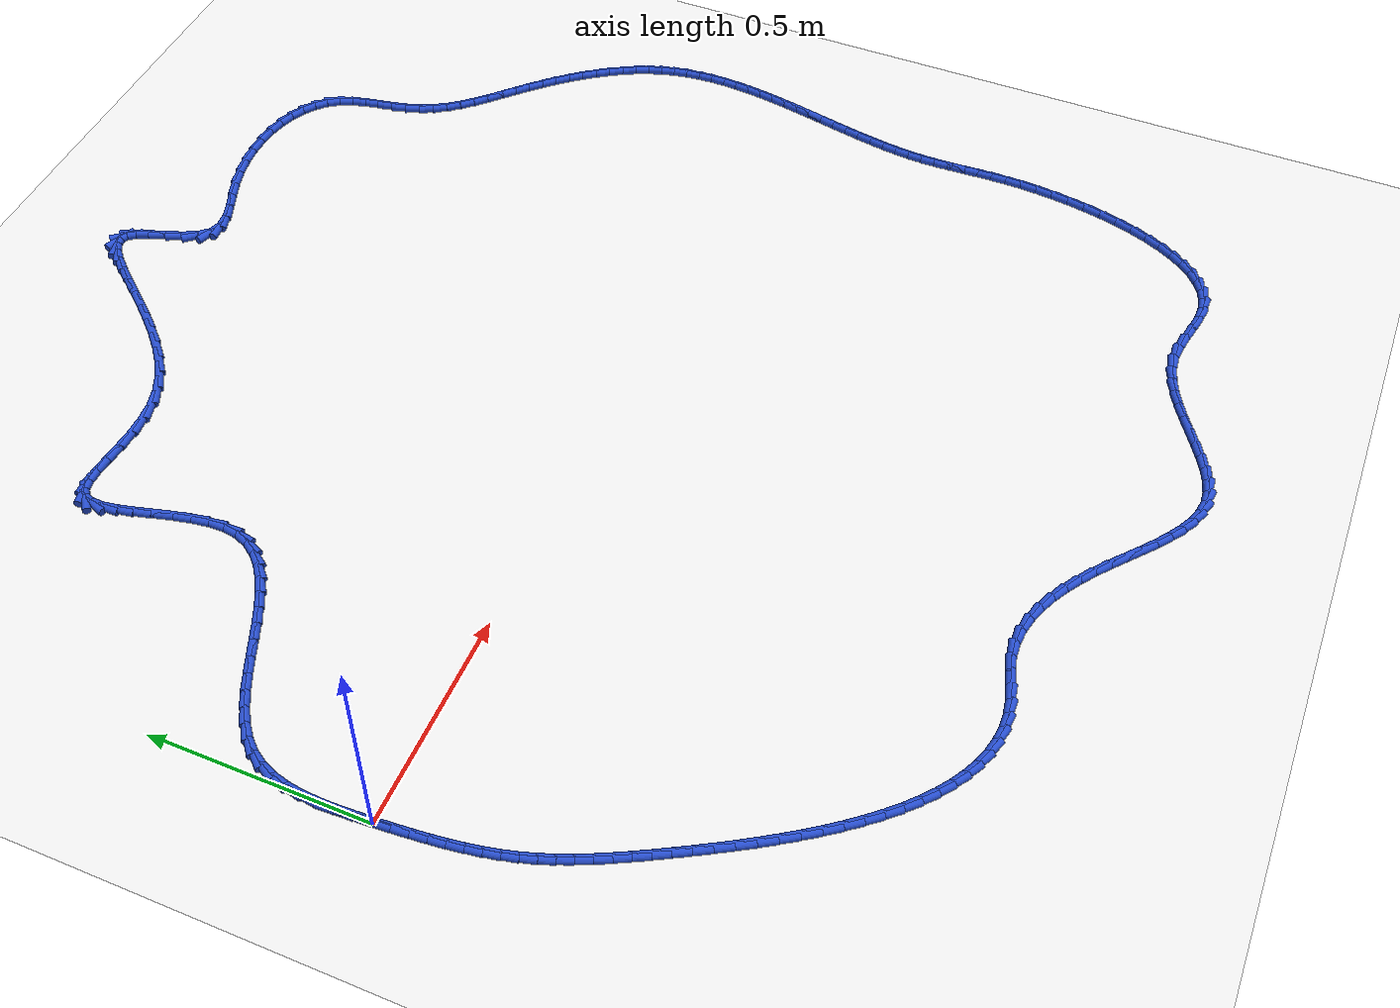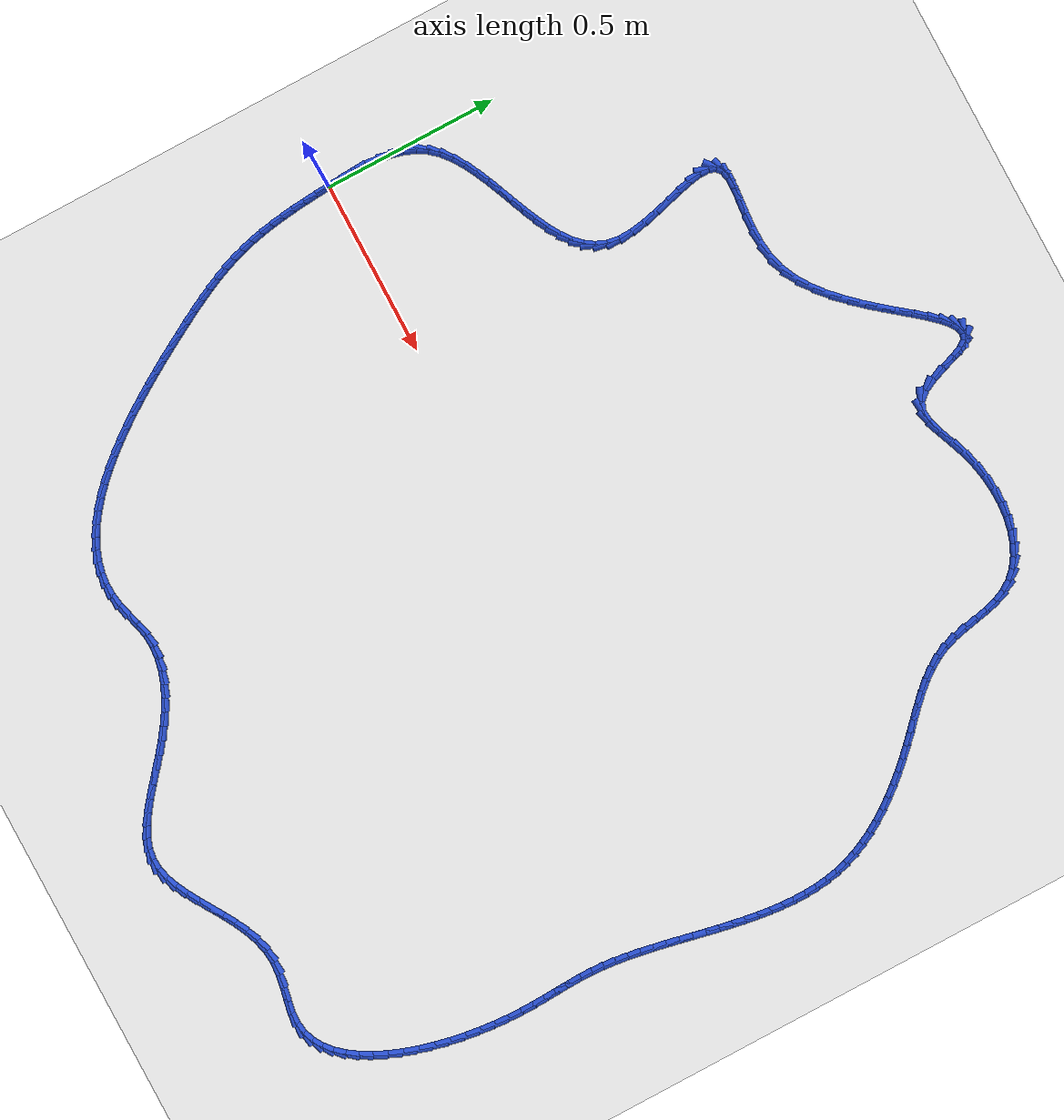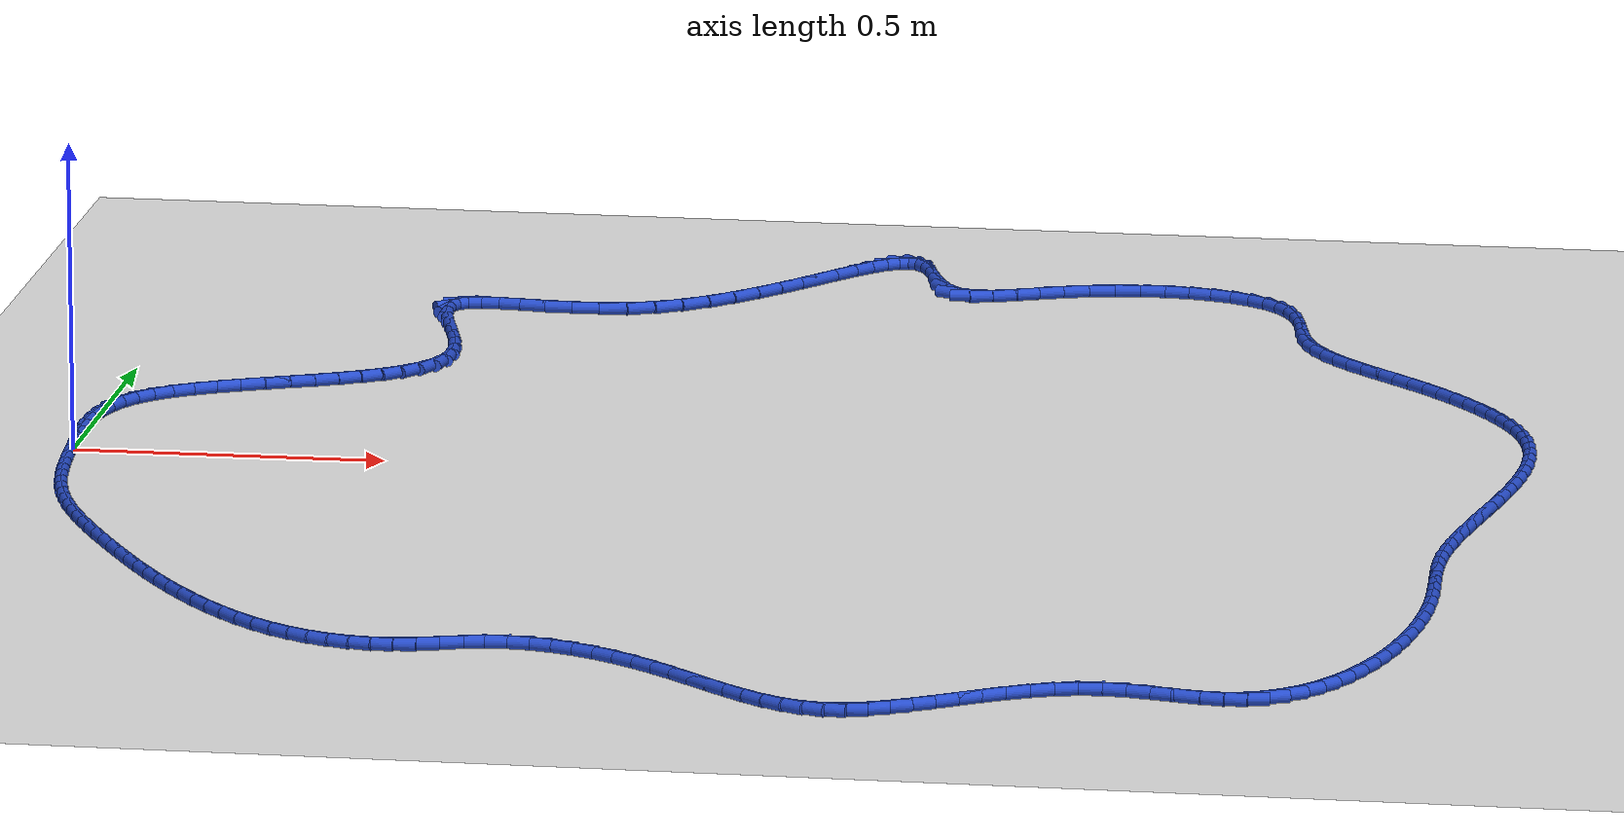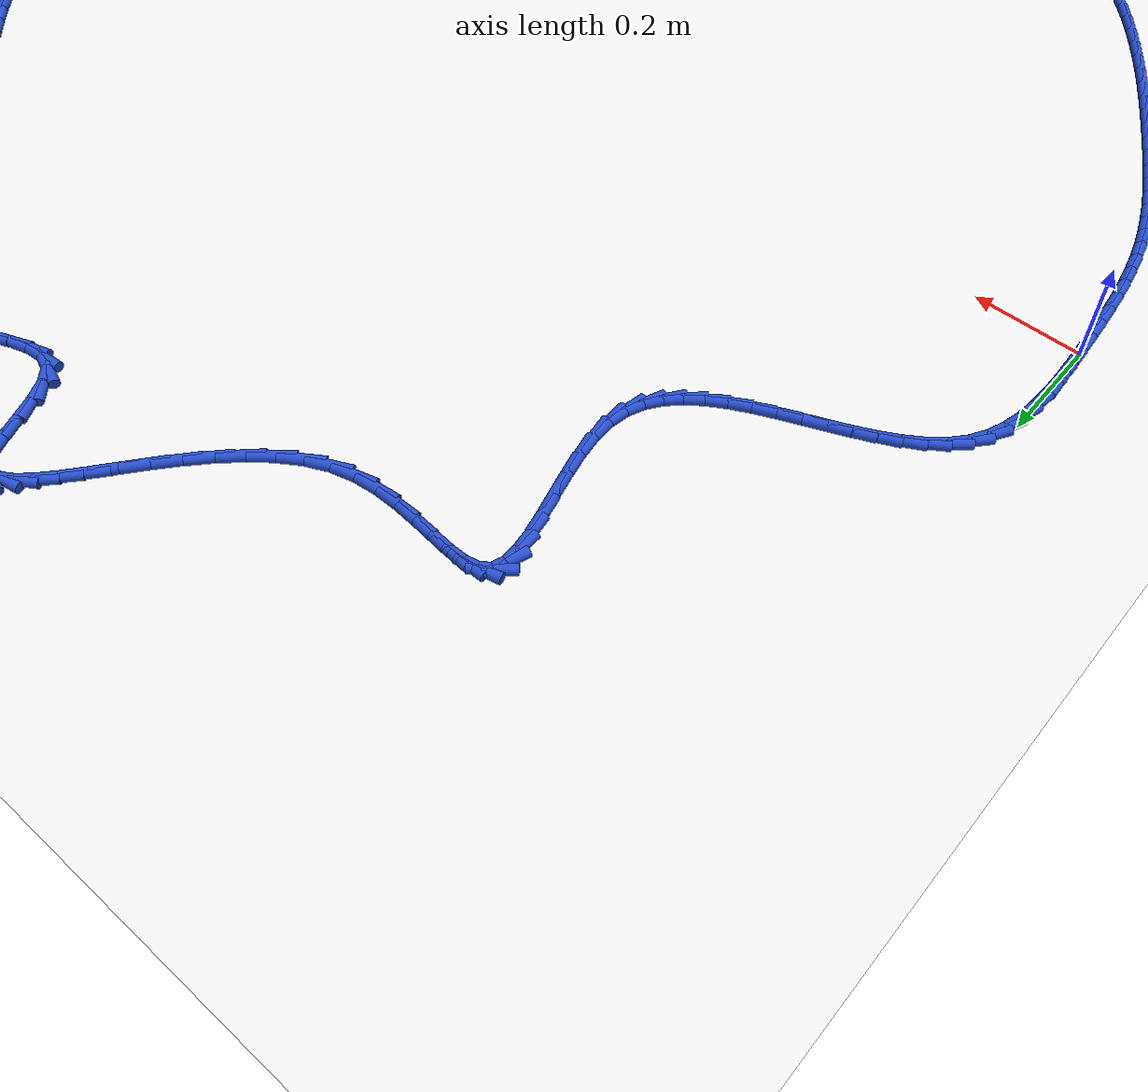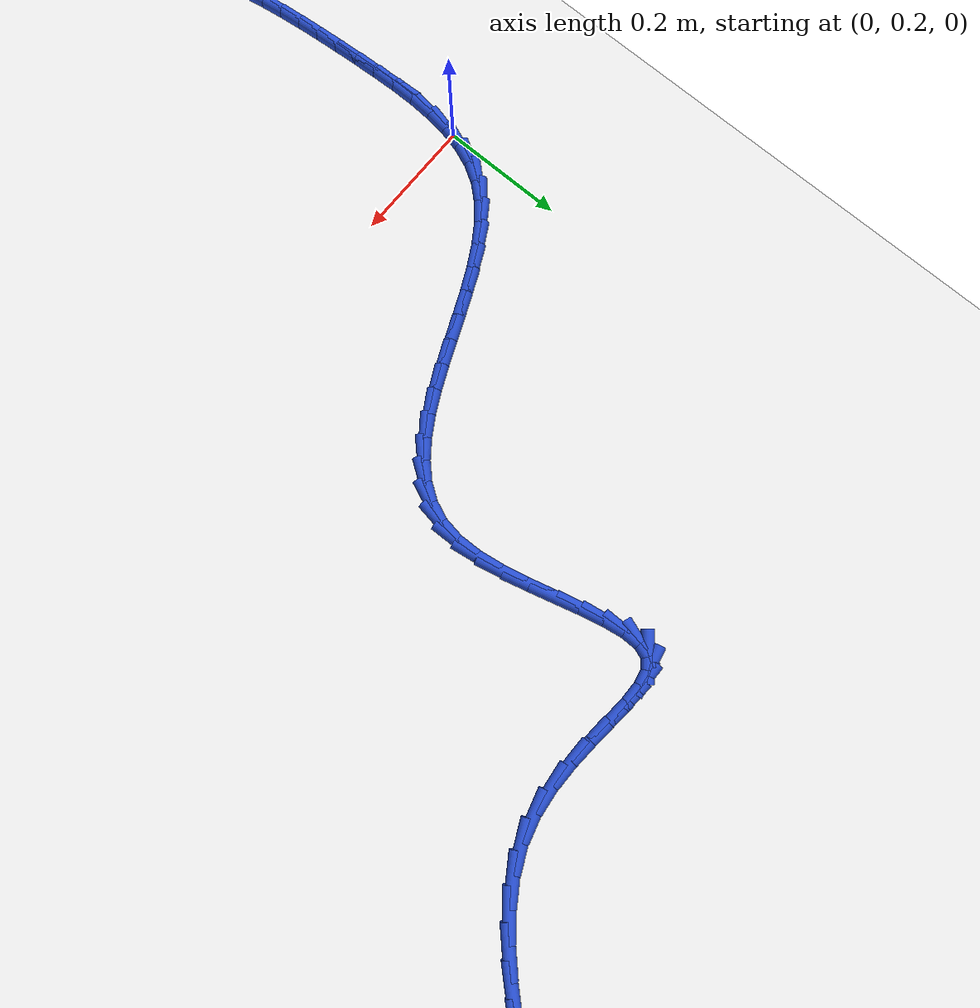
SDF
<sdf version="1.6">
 <world name="default">
  <light name="sun" type="directional">
   <pose>0 0 10 0 -0 0</pose>
   <diffuse>0.8 0.8 0.8 1</diffuse>
   <specular>0.2 0.2 0.2 1</specular>
   <attenuation>
    <range>1000</range>
    <constant>0.9</constant>
    <linear>0.01</linear>
    <quadratic>0.001</quadratic>
   </attenuation>
   <direction>-0.5 0.1 -0.9</direction>
  </light>
  <model name="ground_plane">
   <static>1</static>
   <link name="link">
    <collision name="collision">
     <geometry><plane><normal>0 0 1</normal><size>100 100</size></plane></geometry>
     <surface><friction><ode><mu>100</mu><mu2>50</mu2></ode></friction></surface>
    </collision>
    <visual name="visual">
     <cast_shadows>0</cast_shadows>
     <geometry><plane><normal>0 0 1</normal><size>100 100</size></plane></geometry>
     <material>
      <script><uri>file://media/materials/scripts/gazebo.material</uri><name>Gazebo/WhiteGlow</name></script>
     </material>
    </visual>
   </link>
  </model>
  <gravity>0 0 -9.8</gravity>
  <magnetic_field>6e-06 2.3e-05 -4.2e-05</magnetic_field>
  <atmosphere type="adiabatic"/>
  <physics name="default_physics" default="0" type="ode">
   <max_step_size>0.001</max_step_size>
   <real_time_factor>1</real_time_factor>
   <real_time_update_rate>1000</real_time_update_rate>
  </physics>
  <scene><ambient>0.4 0.4 0.4 1</ambient><background>0.7 0.7 0.7 1</background><shadows>1</shadows></scene>
  <spherical_coordinates>
   <surface_model>EARTH_WGS84</surface_model>
   <latitude_deg>0</latitude_deg>
   <longitude_deg>0</longitude_deg>
   <elevation>0</elevation>
   <heading_deg>0</heading_deg>
  </spherical_coordinates>
  <model name="line">
   <link name="link_0">
    <pose>1.0842021724855044e-17 3.469446951953614e-17 0.01 0 1.57 -1.508970521655884</pose>
    <collision name="collision">
     <geometry><cylinder><radius>0.01</radius><length>0.08</length></cylinder></geometry>
    </collision>
    <visual name="visual">
     <material>
      <script><name>Gazebo/Blue</name><uri>file://media/materials/scripts/gazebo.material</uri></script>
     </material>
     <geometry><cylinder><radius>0.01</radius><length>0.08</length></cylinder></geometry>
    </visual>
   </link>
   <link name="link_1">
    <pose>-0.0023725725082027927 0.038326209172052955 0.01 0 1.57 -1.5306018567062096</pose>
    <collision name="collision">
     <geometry><cylinder><radius>0.01</radius><length>0.08</length></cylinder></geometry>
    </collision>
    <visual name="visual">
     <material>
      <script><name>Gazebo/Blue</name><uri>file://media/materials/scripts/gazebo.material</uri></script>
     </material>
     <geometry><cylinder><radius>0.01</radius><length>0.08</length></cylinder></geometry>
    </visual>
   </link>
   <link name="link_2">
    <pose>-0.003921483617635873 0.0768408824159212 0.01 0 1.57 -1.56924784026682</pose>
    <collision name="collision">
     <geometry><cylinder><radius>0.01</radius><length>0.08</length></cylinder></geometry>
    </collision>
    <visual name="visual">
     <material>
      <script><name>Gazebo/Blue</name><uri>file://media/materials/scripts/gazebo.material</uri></script>
     </material>
     <geometry><cylinder><radius>0.01</radius><length>0.08</length></cylinder></geometry>
    </visual>
   </link>
   <link name="link_3">
    <pose>-0.00398061436574998 0.11502700788780326 0.01 0 1.57 1.514702668155014</pose>
    <collision name="collision">
     <geometry><cylinder><radius>0.01</radius><length>0.08</length></cylinder></geometry>
    </collision>
    <visual name="visual">
     <material>
      <script><name>Gazebo/Blue</name><uri>file://media/materials/scripts/gazebo.material</uri></script>
     </material>
     <geometry><cylinder><radius>0.01</radius><length>0.08</length></cylinder></geometry>
    </visual>
   </link>
   <link name="link_4">
    <pose>-0.0018838457899958598 0.15236757374389748 0.01 0 1.57 1.4349221693202618</pose>
    <collision name="collision">
     <geometry><cylinder><radius>0.01</radius><length>0.08</length></cylinder></geometry>
    </collision>
    <visual name="visual">
     <material>
      <script><name>Gazebo/Blue</name><uri>file://media/materials/scripts/gazebo.material</uri></script>
     </material>
     <geometry><cylinder><radius>0.01</radius><length>0.08</length></cylinder></geometry>
    </visual>
   </link>
   <link name="link_5">
    <pose>0.0030349410721757474 0.18834556814040238 0.01 0 1.57 1.3290684312264622</pose>
    <collision name="collision">
     <geometry><cylinder><radius>0.01</radius><length>0.08</length></cylinder></geometry>
    </collision>
    <visual name="visual">
     <material>
      <script><name>Gazebo/Blue</name><uri>file://media/materials/scripts/gazebo.material</uri></script>
     </material>
     <geometry><cylinder><radius>0.01</radius><length>0.08</length></cylinder></geometry>
    </visual>
   </link>
   <link name="link_6">
    <pose>0.01144186518331409 0.2224439792335163 0.01 0 1.57 1.1935449923174148</pose>
    <collision name="collision">
     <geometry><cylinder><radius>0.01</radius><length>0.08</length></cylinder></geometry>
    </collision>
    <visual name="visual">
     <material>
      <script><name>Gazebo/Blue</name><uri>file://media/materials/scripts/gazebo.material</uri></script>
     </material>
     <geometry><cylinder><radius>0.01</radius><length>0.08</length></cylinder></geometry>
    </visual>
   </link>
   <link name="link_7">
    <pose>0.024003045505968407 0.2541457951794377 0.01 0 1.57 1.0276076320988994</pose>
    <collision name="collision">
     <geometry><cylinder><radius>0.01</radius><length>0.08</length></cylinder></geometry>
    </collision>
    <visual name="visual">
     <material>
      <script><name>Gazebo/Blue</name><uri>file://media/materials/scripts/gazebo.material</uri></script>
     </material>
     <geometry><cylinder><radius>0.01</radius><length>0.08</length></cylinder></geometry>
    </visual>
   </link>
   <link name="link_8">
    <pose>0.041384579762039464 0.282934018649209 0.01 0 1.57 0.8468864799070612</pose>
    <collision name="collision">
     <geometry><cylinder><radius>0.01</radius><length>0.08</length></cylinder></geometry>
    </collision>
    <visual name="visual">
     <material>
      <script><name>Gazebo/Blue</name><uri>file://media/materials/scripts/gazebo.material</uri></script>
     </material>
     <geometry><cylinder><radius>0.01</radius><length>0.08</length></cylinder></geometry>
    </visual>
   </link>
   <link name="link_9">
    <pose>0.06397103292938895 0.30848403833366683 0.01 0 1.57 0.6948237427598828</pose>
    <collision name="collision">
     <geometry><cylinder><radius>0.01</radius><length>0.08</length></cylinder></geometry>
    </collision>
    <visual name="visual">
     <material>
      <script><name>Gazebo/Blue</name><uri>file://media/materials/scripts/gazebo.material</uri></script>
     </material>
     <geometry><cylinder><radius>0.01</radius><length>0.08</length></cylinder></geometry>
    </visual>
   </link>
   <link name="link_10">
    <pose>0.09116015980688535 0.33114558182968595 0.01 0 1.57 0.5794943225564692</pose>
    <collision name="collision">
     <geometry><cylinder><radius>0.01</radius><length>0.08</length></cylinder></geometry>
    </collision>
    <visual name="visual">
     <material>
      <script><name>Gazebo/Blue</name><uri>file://media/materials/scripts/gazebo.material</uri></script>
     </material>
     <geometry><cylinder><radius>0.01</radius><length>0.08</length></cylinder></geometry>
    </visual>
   </link>
   <link name="link_11">
    <pose>0.12213362629826381 0.35141604155586004 0.01 0 1.57 0.49626071830486734</pose>
    <collision name="collision">
     <geometry><cylinder><radius>0.01</radius><length>0.08</length></cylinder></geometry>
    </collision>
    <visual name="visual">
     <material>
      <script><name>Gazebo/Blue</name><uri>file://media/materials/scripts/gazebo.material</uri></script>
     </material>
     <geometry><cylinder><radius>0.01</radius><length>0.08</length></cylinder></geometry>
    </visual>
   </link>
   <link name="link_12">
    <pose>0.15607309830725968 0.36979280993078245 0.01 0 1.57 0.4398036585615957</pose>
    <collision name="collision">
     <geometry><cylinder><radius>0.01</radius><length>0.08</length></cylinder></geometry>
    </collision>
    <visual name="visual">
     <material>
      <script><name>Gazebo/Blue</name><uri>file://media/materials/scripts/gazebo.material</uri></script>
     </material>
     <geometry><cylinder><radius>0.01</radius><length>0.08</length></cylinder></geometry>
    </visual>
   </link>
   <link name="link_13">
    <pose>0.19216024173760793 0.3867732793730467 0.01 0 1.57 0.4059283418044757</pose>
    <collision name="collision">
     <geometry><cylinder><radius>0.01</radius><length>0.08</length></cylinder></geometry>
    </collision>
    <visual name="visual">
     <material>
      <script><name>Gazebo/Blue</name><uri>file://media/materials/scripts/gazebo.material</uri></script>
     </material>
     <geometry><cylinder><radius>0.01</radius><length>0.08</length></cylinder></geometry>
    </visual>
   </link>
   <link name="link_14">
    <pose>0.22957672249304376 0.4028548423012461 0.01 0 1.57 0.39202308413880016</pose>
    <collision name="collision">
     <geometry><cylinder><radius>0.01</radius><length>0.08</length></cylinder></geometry>
    </collision>
    <visual name="visual">
     <material>
      <script><name>Gazebo/Blue</name><uri>file://media/materials/scripts/gazebo.material</uri></script>
     </material>
     <geometry><cylinder><radius>0.01</radius><length>0.08</length></cylinder></geometry>
    </visual>
   </link>
   <link name="link_15">
    <pose>0.2675042064773025 0.4185348911339744 0.01 0 1.57 0.3970734300450248</pose>
    <collision name="collision">
     <geometry><cylinder><radius>0.01</radius><length>0.08</length></cylinder></geometry>
    </collision>
    <visual name="visual">
     <material>
      <script><name>Gazebo/Blue</name><uri>file://media/materials/scripts/gazebo.material</uri></script>
     </material>
     <geometry><cylinder><radius>0.01</radius><length>0.08</length></cylinder></geometry>
    </visual>
   </link>
   <link name="link_16">
    <pose>0.3051243595941192 0.4343108182898249 0.01 0 1.57 0.42163821745616825</pose>
    <collision name="collision">
     <geometry><cylinder><radius>0.01</radius><length>0.08</length></cylinder></geometry>
    </collision>
    <visual name="visual">
     <material>
      <script><name>Gazebo/Blue</name><uri>file://media/materials/scripts/gazebo.material</uri></script>
     </material>
     <geometry><cylinder><radius>0.01</radius><length>0.08</length></cylinder></geometry>
    </visual>
   </link>
   <link name="link_17">
    <pose>0.34161884774722917 0.4506800161873912 0.01 0 1.57 0.4679131728103945</pose>
    <collision name="collision">
     <geometry><cylinder><radius>0.01</radius><length>0.08</length></cylinder></geometry>
    </collision>
    <visual name="visual">
     <material>
      <script><name>Gazebo/Blue</name><uri>file://media/materials/scripts/gazebo.material</uri></script>
     </material>
     <geometry><cylinder><radius>0.01</radius><length>0.08</length></cylinder></geometry>
    </visual>
   </link>
   <link name="link_18">
    <pose>0.37616933684036724 0.46813987724526657 0.01 0 1.57 0.5398415569391267</pose>
    <collision name="collision">
     <geometry><cylinder><radius>0.01</radius><length>0.08</length></cylinder></geometry>
    </collision>
    <visual name="visual">
     <material>
      <script><name>Gazebo/Blue</name><uri>file://media/materials/scripts/gazebo.material</uri></script>
     </material>
     <geometry><cylinder><radius>0.01</radius><length>0.08</length></cylinder></geometry>
    </visual>
   </link>
   <link name="link_19">
    <pose>0.40795749277726895 0.4871877938820446 0.01 0 1.57 0.6429960444797768</pose>
    <collision name="collision">
     <geometry><cylinder><radius>0.01</radius><length>0.08</length></cylinder></geometry>
    </collision>
    <visual name="visual">
     <material>
      <script><name>Gazebo/Blue</name><uri>file://media/materials/scripts/gazebo.material</uri></script>
     </material>
     <geometry><cylinder><radius>0.01</radius><length>0.08</length></cylinder></geometry>
    </visual>
   </link>
   <link name="link_20">
    <pose>0.43616498146166943 0.5083211585163189 0.01 0 1.57 0.7834563902968918</pose>
    <collision name="collision">
     <geometry><cylinder><radius>0.01</radius><length>0.08</length></cylinder></geometry>
    </collision>
    <visual name="visual">
     <material>
      <script><name>Gazebo/Blue</name><uri>file://media/materials/scripts/gazebo.material</uri></script>
     </material>
     <geometry><cylinder><radius>0.01</radius><length>0.08</length></cylinder></geometry>
    </visual>
   </link>
   <link name="link_21">
    <pose>0.4599734687973036 0.5320373635666827 0.01 0 1.57 0.9642490270680982</pose>
    <collision name="collision">
     <geometry><cylinder><radius>0.01</radius><length>0.08</length></cylinder></geometry>
    </collision>
    <visual name="visual">
     <material>
      <script><name>Gazebo/Blue</name><uri>file://media/materials/scripts/gazebo.material</uri></script>
     </material>
     <geometry><cylinder><radius>0.01</radius><length>0.08</length></cylinder></geometry>
    </visual>
   </link>
   <link name="link_22">
    <pose>0.47856462068790695 0.5588338014517298 0.01 0 1.57 1.178824349810268</pose>
    <collision name="collision">
     <geometry><cylinder><radius>0.01</radius><length>0.08</length></cylinder></geometry>
    </collision>
    <visual name="visual">
     <material>
      <script><name>Gazebo/Blue</name><uri>file://media/materials/scripts/gazebo.material</uri></script>
     </material>
     <geometry><cylinder><radius>0.01</radius><length>0.08</length></cylinder></geometry>
    </visual>
   </link>
   <link name="link_23">
    <pose>0.4911201030372145 0.5892078645900533 0.01 0 1.57 1.406337395249148</pose>
    <collision name="collision">
     <geometry><cylinder><radius>0.01</radius><length>0.08</length></cylinder></geometry>
    </collision>
    <visual name="visual">
     <material>
      <script><name>Gazebo/Blue</name><uri>file://media/materials/scripts/gazebo.material</uri></script>
     </material>
     <geometry><cylinder><radius>0.01</radius><length>0.08</length></cylinder></geometry>
    </visual>
   </link>
   <link name="link_24">
    <pose>0.4968355066237401 0.62364675279365 0.01 0 1.57 -1.5446382106421586</pose>
    <collision name="collision">
     <geometry><cylinder><radius>0.01</radius><length>0.08</length></cylinder></geometry>
    </collision>
    <visual name="visual">
     <material>
      <script><name>Gazebo/Blue</name><uri>file://media/materials/scripts/gazebo.material</uri></script>
     </material>
     <geometry><cylinder><radius>0.01</radius><length>0.08</length></cylinder></geometry>
    </visual>
   </link>
   <link name="link_25">
    <pose>0.4958330920820593 0.6619593702748817 0.01 0 1.57 -1.4225984590854381</pose>
    <collision name="collision">
     <geometry><cylinder><radius>0.01</radius><length>0.08</length></cylinder></geometry>
    </collision>
    <visual name="visual">
     <material>
      <script><name>Gazebo/Blue</name><uri>file://media/materials/scripts/gazebo.material</uri></script>
     </material>
     <geometry><cylinder><radius>0.01</radius><length>0.08</length></cylinder></geometry>
    </visual>
   </link>
   <link name="link_26">
    <pose>0.489726493270545 0.7028629790733343 0.01 0 1.57 -1.3497811578116319</pose>
    <collision name="collision">
     <geometry><cylinder><radius>0.01</radius><length>0.08</length></cylinder></geometry>
    </collision>
    <visual name="visual">
     <material>
      <script><name>Gazebo/Blue</name><uri>file://media/materials/scripts/gazebo.material</uri></script>
     </material>
     <geometry><cylinder><radius>0.01</radius><length>0.08</length></cylinder></geometry>
    </visual>
   </link>
   <link name="link_27">
    <pose>0.48026428938357973 0.7449760651358923 0.01 0 1.57 -1.3127566995425688</pose>
    <collision name="collision">
     <geometry><cylinder><radius>0.01</radius><length>0.08</length></cylinder></geometry>
    </collision>
    <visual name="visual">
     <material>
      <script><name>Gazebo/Blue</name><uri>file://media/materials/scripts/gazebo.material</uri></script>
     </material>
     <geometry><cylinder><radius>0.01</radius><length>0.08</length></cylinder></geometry>
    </visual>
   </link>
   <link name="link_28">
    <pose>0.46919505961554586 0.7869171144094399 0.01 0 1.57 -1.3065525828894573</pose>
    <collision name="collision">
     <geometry><cylinder><radius>0.01</radius><length>0.08</length></cylinder></geometry>
    </collision>
    <visual name="visual">
     <material>
      <script><name>Gazebo/Blue</name><uri>file://media/materials/scripts/gazebo.material</uri></script>
     </material>
     <geometry><cylinder><radius>0.01</radius><length>0.08</length></cylinder></geometry>
    </visual>
   </link>
   <link name="link_29">
    <pose>0.45826738316082577 0.8273046128408612 0.01 0 1.57 -1.3340156547822672</pose>
    <collision name="collision">
     <geometry><cylinder><radius>0.01</radius><length>0.08</length></cylinder></geometry>
    </collision>
    <visual name="visual">
     <material>
      <script><name>Gazebo/Blue</name><uri>file://media/materials/scripts/gazebo.material</uri></script>
     </material>
     <geometry><cylinder><radius>0.01</radius><length>0.08</length></cylinder></geometry>
    </visual>
   </link>
   <link name="link_30">
    <pose>0.44922983921380194 0.8647570463770412 0.01 0 1.57 -1.4092852941443799</pose>
    <collision name="collision">
     <geometry><cylinder><radius>0.01</radius><length>0.08</length></cylinder></geometry>
    </collision>
    <visual name="visual">
     <material>
      <script><name>Gazebo/Blue</name><uri>file://media/materials/scripts/gazebo.material</uri></script>
     </material>
     <geometry><cylinder><radius>0.01</radius><length>0.08</length></cylinder></geometry>
    </visual>
   </link>
   <link name="link_31">
    <pose>0.44383100696885686 0.8978929009648635 0.01 0 1.57 -1.5703756894274108</pose>
    <collision name="collision">
     <geometry><cylinder><radius>0.01</radius><length>0.08</length></cylinder></geometry>
    </collision>
    <visual name="visual">
     <material>
      <script><name>Gazebo/Blue</name><uri>file://media/materials/scripts/gazebo.material</uri></script>
     </material>
     <geometry><cylinder><radius>0.01</radius><length>0.08</length></cylinder></geometry>
    </visual>
   </link>
   <link name="link_32">
    <pose>0.4438194656203728 0.9253306625512129 0.01 0 1.57 1.2341663769417444</pose>
    <collision name="collision">
     <geometry><cylinder><radius>0.01</radius><length>0.08</length></cylinder></geometry>
    </collision>
    <visual name="visual">
     <material>
      <script><name>Gazebo/Blue</name><uri>file://media/materials/scripts/gazebo.material</uri></script>
     </material>
     <geometry><cylinder><radius>0.01</radius><length>0.08</length></cylinder></geometry>
    </visual>
   </link>
   <link name="link_33">
    <pose>0.45094379436273235 0.9456888170829736 0.01 0 1.57 0.6629433262610746</pose>
    <collision name="collision">
     <geometry><cylinder><radius>0.01</radius><length>0.08</length></cylinder></geometry>
    </collision>
    <visual name="visual">
     <material>
      <script><name>Gazebo/Blue</name><uri>file://media/materials/scripts/gazebo.material</uri></script>
     </material>
     <geometry><cylinder><radius>0.01</radius><length>0.08</length></cylinder></geometry>
    </visual>
   </link>
   <link name="link_34">
    <pose>0.4666322199821111 0.9579388407464322 0.01 0 1.57 0.21961172141788254</pose>
    <collision name="collision">
     <geometry><cylinder><radius>0.01</radius><length>0.08</length></cylinder></geometry>
    </collision>
    <visual name="visual">
     <material>
      <script><name>Gazebo/Blue</name><uri>file://media/materials/scripts/gazebo.material</uri></script>
     </material>
     <geometry><cylinder><radius>0.01</radius><length>0.08</length></cylinder></geometry>
    </visual>
   </link>
   <link name="link_35">
    <pose>0.49033659723340095 0.9632299365643225 0.01 0 1.57 0.010225169959654248</pose>
    <collision name="collision">
     <geometry><cylinder><radius>0.01</radius><length>0.08</length></cylinder></geometry>
    </collision>
    <visual name="visual">
     <material>
      <script><name>Gazebo/Blue</name><uri>file://media/materials/scripts/gazebo.material</uri></script>
     </material>
     <geometry><cylinder><radius>0.01</radius><length>0.08</length></cylinder></geometry>
    </visual>
   </link>
   <link name="link_36">
    <pose>0.520755812561147 0.963540989051768 0.01 0 1.57 -0.07489083612325771</pose>
    <collision name="collision">
     <geometry><cylinder><radius>0.01</radius><length>0.08</length></cylinder></geometry>
    </collision>
    <visual name="visual">
     <material>
      <script><name>Gazebo/Blue</name><uri>file://media/materials/scripts/gazebo.material</uri></script>
     </material>
     <geometry><cylinder><radius>0.01</radius><length>0.08</length></cylinder></geometry>
    </visual>
   </link>
   <link name="link_37">
    <pose>0.5565872729485545 0.9608525129142669 0.01 0 1.57 -0.09255867676396555</pose>
    <collision name="collision">
     <geometry><cylinder><radius>0.01</radius><length>0.08</length></cylinder></geometry>
    </collision>
    <visual name="visual">
     <material>
      <script><name>Gazebo/Blue</name><uri>file://media/materials/scripts/gazebo.material</uri></script>
     </material>
     <geometry><cylinder><radius>0.01</radius><length>0.08</length></cylinder></geometry>
    </visual>
   </link>
   <link name="link_38">
    <pose>0.5965283853788292 0.9571450228573182 0.01 0 1.57 -0.06414827956842307</pose>
    <collision name="collision">
     <geometry><cylinder><radius>0.01</radius><length>0.08</length></cylinder></geometry>
    </collision>
    <visual name="visual">
     <material>
      <script><name>Gazebo/Blue</name><uri>file://media/materials/scripts/gazebo.material</uri></script>
     </material>
     <geometry><cylinder><radius>0.01</radius><length>0.08</length></cylinder></geometry>
    </visual>
   </link>
   <link name="link_39">
    <pose>0.6392765568351774 0.954399033586421 0.01 0 1.57 0.004429678087722703</pose>
    <collision name="collision">
     <geometry><cylinder><radius>0.01</radius><length>0.08</length></cylinder></geometry>
    </collision>
    <visual name="visual">
     <material>
      <script><name>Gazebo/Blue</name><uri>file://media/materials/scripts/gazebo.material</uri></script>
     </material>
     <geometry><cylinder><radius>0.01</radius><length>0.08</length></cylinder></geometry>
    </visual>
   </link>
   <link name="link_40">
    <pose>0.6835291943008039 0.9545950598070734 0.01 0 1.57 0.11463661992983007</pose>
    <collision name="collision">
     <geometry><cylinder><radius>0.01</radius><length>0.08</length></cylinder></geometry>
    </collision>
    <visual name="visual">
     <material>
      <script><name>Gazebo/Blue</name><uri>file://media/materials/scripts/gazebo.material</uri></script>
     </material>
     <geometry><cylinder><radius>0.01</radius><length>0.08</length></cylinder></geometry>
    </visual>
   </link>
   <link name="link_41">
    <pose>0.7279837047589144 0.9597136162247737 0.01 0 1.57 0.26995627589608795</pose>
    <collision name="collision">
     <geometry><cylinder><radius>0.01</radius><length>0.08</length></cylinder></geometry>
    </collision>
    <visual name="visual">
     <material>
      <script><name>Gazebo/Blue</name><uri>file://media/materials/scripts/gazebo.material</uri></script>
     </material>
     <geometry><cylinder><radius>0.01</radius><length>0.08</length></cylinder></geometry>
    </visual>
   </link>
   <link name="link_42">
    <pose>0.7713462963367079 0.9717125250472792 0.01 0 1.57 0.4408642306535517</pose>
    <collision name="collision">
     <geometry><cylinder><radius>0.01</radius><length>0.08</length></cylinder></geometry>
    </collision>
    <visual name="visual">
     <material>
      <script><name>Gazebo/Blue</name><uri>file://media/materials/scripts/gazebo.material</uri></script>
     </material>
     <geometry><cylinder><radius>0.01</radius><length>0.08</length></cylinder></geometry>
    </visual>
   </link>
   <link name="link_43">
    <pose>0.8128158296628959 0.9912793740915068 0.01 0 1.57 0.5802218542452423</pose>
    <collision name="collision">
     <geometry><cylinder><radius>0.01</radius><length>0.08</length></cylinder></geometry>
    </collision>
    <visual name="visual">
     <material>
      <script><name>Gazebo/Blue</name><uri>file://media/materials/scripts/gazebo.material</uri></script>
     </material>
     <geometry><cylinder><radius>0.01</radius><length>0.08</length></cylinder></geometry>
    </visual>
   </link>
   <link name="link_44">
    <pose>0.8523350801038764 1.0171836728519135 0.01 0 1.57 0.6874824626980587</pose>
    <collision name="collision">
     <geometry><cylinder><radius>0.01</radius><length>0.08</length></cylinder></geometry>
    </collision>
    <visual name="visual">
     <material>
      <script><name>Gazebo/Blue</name><uri>file://media/materials/scripts/gazebo.material</uri></script>
     </material>
     <geometry><cylinder><radius>0.01</radius><length>0.08</length></cylinder></geometry>
    </visual>
   </link>
   <link name="link_45">
    <pose>0.8899085677124742 1.0480357309327468 0.01 0 1.57 0.7679516693271748</pose>
    <collision name="collision">
     <geometry><cylinder><radius>0.01</radius><length>0.08</length></cylinder></geometry>
    </collision>
    <visual name="visual">
     <material>
      <script><name>Gazebo/Blue</name><uri>file://media/materials/scripts/gazebo.material</uri></script>
     </material>
     <geometry><cylinder><radius>0.01</radius><length>0.08</length></cylinder></geometry>
    </visual>
   </link>
   <link name="link_46">
    <pose>0.9255408125415151 1.0824458579382545 0.01 0 1.57 0.8264000494082598</pose>
    <collision name="collision">
     <geometry><cylinder><radius>0.01</radius><length>0.08</length></cylinder></geometry>
    </collision>
    <visual name="visual">
     <material>
      <script><name>Gazebo/Blue</name><uri>file://media/materials/scripts/gazebo.material</uri></script>
     </material>
     <geometry><cylinder><radius>0.01</radius><length>0.08</length></cylinder></geometry>
    </visual>
   </link>
   <link name="link_47">
    <pose>0.9592363346438242 1.1190243634726846 0.01 0 1.57 0.8661514637370296</pose>
    <collision name="collision">
     <geometry><cylinder><radius>0.01</radius><length>0.08</length></cylinder></geometry>
    </collision>
    <visual name="visual">
     <material>
      <script><name>Gazebo/Blue</name><uri>file://media/materials/scripts/gazebo.material</uri></script>
     </material>
     <geometry><cylinder><radius>0.01</radius><length>0.08</length></cylinder></geometry>
    </visual>
   </link>
   <link name="link_48">
    <pose>0.9909996540722263 1.1563815571402838 0.01 0 1.57 0.8888182619212447</pose>
    <collision name="collision">
     <geometry><cylinder><radius>0.01</radius><length>0.08</length></cylinder></geometry>
    </collision>
    <visual name="visual">
     <material>
      <script><name>Gazebo/Blue</name><uri>file://media/materials/scripts/gazebo.material</uri></script>
     </material>
     <geometry><cylinder><radius>0.01</radius><length>0.08</length></cylinder></geometry>
    </visual>
   </link>
   <link name="link_49">
    <pose>1.0208352908795475 1.1931277485453007 0.01 0 1.57 0.8940216726257181</pose>
    <collision name="collision">
     <geometry><cylinder><radius>0.01</radius><length>0.08</length></cylinder></geometry>
    </collision>
    <visual name="visual">
     <material>
      <script><name>Gazebo/Blue</name><uri>file://media/materials/scripts/gazebo.material</uri></script>
     </material>
     <geometry><cylinder><radius>0.01</radius><length>0.08</length></cylinder></geometry>
    </visual>
   </link>
   <link name="link_50">
    <pose>1.048747765118613 1.2278732472919827 0.01 0 1.57 0.8786125514776213</pose>
    <collision name="collision">
     <geometry><cylinder><radius>0.01</radius><length>0.08</length></cylinder></geometry>
    </collision>
    <visual name="visual">
     <material>
      <script><name>Gazebo/Blue</name><uri>file://media/materials/scripts/gazebo.material</uri></script>
     </material>
     <geometry><cylinder><radius>0.01</radius><length>0.08</length></cylinder></geometry>
    </visual>
   </link>
   <link name="link_51">
    <pose>1.0747415968422473 1.2592283629845769 0.01 0 1.57 0.8346199513677026</pose>
    <collision name="collision">
     <geometry><cylinder><radius>0.01</radius><length>0.08</length></cylinder></geometry>
    </collision>
    <visual name="visual">
     <material>
      <script><name>Gazebo/Blue</name><uri>file://media/materials/scripts/gazebo.material</uri></script>
     </material>
     <geometry><cylinder><radius>0.01</radius><length>0.08</length></cylinder></geometry>
    </visual>
   </link>
   <link name="link_52">
    <pose>1.0988213061032766 1.2858034052273317 0.01 0 1.57 0.7439700312572795</pose>
    <collision name="collision">
     <geometry><cylinder><radius>0.01</radius><length>0.08</length></cylinder></geometry>
    </collision>
    <visual name="visual">
     <material>
      <script><name>Gazebo/Blue</name><uri>file://media/materials/scripts/gazebo.material</uri></script>
     </material>
     <geometry><cylinder><radius>0.01</radius><length>0.08</length></cylinder></geometry>
    </visual>
   </link>
   <link name="link_53">
    <pose>1.1209914129545258 1.3062086836244946 0.01 0 1.57 0.5649675752953512</pose>
    <collision name="collision">
     <geometry><cylinder><radius>0.01</radius><length>0.08</length></cylinder></geometry>
    </collision>
    <visual name="visual">
     <material>
      <script><name>Gazebo/Blue</name><uri>file://media/materials/scripts/gazebo.material</uri></script>
     </material>
     <geometry><cylinder><radius>0.01</radius><length>0.08</length></cylinder></geometry>
    </visual>
   </link>
   <link name="link_54">
    <pose>1.14125643744882 1.319054507780313 0.01 0 1.57 0.20908482270291834</pose>
    <collision name="collision">
     <geometry><cylinder><radius>0.01</radius><length>0.08</length></cylinder></geometry>
    </collision>
    <visual name="visual">
     <material>
      <script><name>Gazebo/Blue</name><uri>file://media/materials/scripts/gazebo.material</uri></script>
     </material>
     <geometry><cylinder><radius>0.01</radius><length>0.08</length></cylinder></geometry>
    </visual>
   </link>
   <link name="link_55">
    <pose>1.1596208996389854 1.3229511872990352 0.01 0 1.57 -0.3728819351918733</pose>
    <collision name="collision">
     <geometry><cylinder><radius>0.01</radius><length>0.08</length></cylinder></geometry>
    </collision>
    <visual name="visual">
     <material>
      <script><name>Gazebo/Blue</name><uri>file://media/materials/scripts/gazebo.material</uri></script>
     </material>
     <geometry><cylinder><radius>0.01</radius><length>0.08</length></cylinder></geometry>
    </visual>
   </link>
   <link name="link_56">
    <pose>1.1760893195778457 1.316509031784908 0.01 0 1.57 -0.8946897747275846</pose>
    <collision name="collision">
     <geometry><cylinder><radius>0.01</radius><length>0.08</length></cylinder></geometry>
    </collision>
    <visual name="visual">
     <material>
      <script><name>Gazebo/Blue</name><uri>file://media/materials/scripts/gazebo.material</uri></script>
     </material>
     <geometry><cylinder><radius>0.01</radius><length>0.08</length></cylinder></geometry>
    </visual>
   </link>
   <link name="link_57">
    <pose>1.1906662993884425 1.2983387304484006 0.01 0 1.57 -1.160216142932323</pose>
    <collision name="collision">
     <geometry><cylinder><radius>0.01</radius><length>0.08</length></cylinder></geometry>
    </collision>
    <visual name="visual">
     <material>
      <script><name>Gazebo/Blue</name><uri>file://media/materials/scripts/gazebo.material</uri></script>
     </material>
     <geometry><cylinder><radius>0.01</radius><length>0.08</length></cylinder></geometry>
    </visual>
   </link>
   <link name="link_58">
    <pose>1.2036650766326744 1.2684785297812609 0.01 0 1.57 -1.2380373773565452</pose>
    <collision name="collision">
     <geometry><cylinder><radius>0.01</radius><length>0.08</length></cylinder></geometry>
    </collision>
    <visual name="visual">
     <material>
      <script><name>Gazebo/Blue</name><uri>file://media/materials/scripts/gazebo.material</uri></script>
     </material>
     <geometry><cylinder><radius>0.01</radius><length>0.08</length></cylinder></geometry>
    </visual>
   </link>
   <link name="link_59">
    <pose>1.2164044828844498 1.2316179342745102 0.01 0 1.57 -1.2196464384357153</pose>
    <collision name="collision">
     <geometry><cylinder><radius>0.01</radius><length>0.08</length></cylinder></geometry>
    </collision>
    <visual name="visual">
     <material>
      <script><name>Gazebo/Blue</name><uri>file://media/materials/scripts/gazebo.material</uri></script>
     </material>
     <geometry><cylinder><radius>0.01</radius><length>0.08</length></cylinder></geometry>
    </visual>
   </link>
   <link name="link_60">
    <pose>1.230407811672967 1.193392163383399 0.01 0 1.57 -1.111571690982287</pose>
    <collision name="collision">
     <geometry><cylinder><radius>0.01</radius><length>0.08</length></cylinder></geometry>
    </collision>
    <visual name="visual">
     <material>
      <script><name>Gazebo/Blue</name><uri>file://media/materials/scripts/gazebo.material</uri></script>
     </material>
     <geometry><cylinder><radius>0.01</radius><length>0.08</length></cylinder></geometry>
    </visual>
   </link>
   <link name="link_61">
    <pose>1.2471983565274267 1.1594364365631769 0.01 0 1.57 -0.8506279636703741</pose>
    <collision name="collision">
     <geometry><cylinder><radius>0.01</radius><length>0.08</length></cylinder></geometry>
    </collision>
    <visual name="visual">
     <material>
      <script><name>Gazebo/Blue</name><uri>file://media/materials/scripts/gazebo.material</uri></script>
     </material>
     <geometry><cylinder><radius>0.01</radius><length>0.08</length></cylinder></geometry>
    </visual>
   </link>
   <link name="link_62">
    <pose>1.268299410977027 1.1353859732690943 0.01 0 1.57 -0.3489514192805825</pose>
    <collision name="collision">
     <geometry><cylinder><radius>0.01</radius><length>0.08</length></cylinder></geometry>
    </collision>
    <visual name="visual">
     <material>
      <script><name>Gazebo/Blue</name><uri>file://media/materials/scripts/gazebo.material</uri></script>
     </material>
     <geometry><cylinder><radius>0.01</radius><length>0.08</length></cylinder></geometry>
    </visual>
   </link>
   <link name="link_63">
    <pose>1.294926438287658 1.1256979783619048 0.01 0 1.57 0.08648744381005208</pose>
    <collision name="collision">
     <geometry><cylinder><radius>0.01</radius><length>0.08</length></cylinder></geometry>
    </collision>
    <visual name="visual">
     <material>
      <script><name>Gazebo/Blue</name><uri>file://media/materials/scripts/gazebo.material</uri></script>
     </material>
     <geometry><cylinder><radius>0.01</radius><length>0.08</length></cylinder></geometry>
    </visual>
   </link>
   <link name="link_64">
    <pose>1.3266269085274736 1.128446527541109 0.01 0 1.57 0.3011649946265975</pose>
    <collision name="collision">
     <geometry><cylinder><radius>0.01</radius><length>0.08</length></cylinder></geometry>
    </collision>
    <visual name="visual">
     <material>
      <script><name>Gazebo/Blue</name><uri>file://media/materials/scripts/gazebo.material</uri></script>
     </material>
     <geometry><cylinder><radius>0.01</radius><length>0.08</length></cylinder></geometry>
    </visual>
   </link>
   <link name="link_65">
    <pose>1.3623859636388538 1.139553761436739 0.01 0 1.57 0.37751398148063653</pose>
    <collision name="collision">
     <geometry><cylinder><radius>0.01</radius><length>0.08</length></cylinder></geometry>
    </collision>
    <visual name="visual">
     <material>
      <script><name>Gazebo/Blue</name><uri>file://media/materials/scripts/gazebo.material</uri></script>
     </material>
     <geometry><cylinder><radius>0.01</radius><length>0.08</length></cylinder></geometry>
    </visual>
   </link>
   <link name="link_66">
    <pose>1.4011883149180222 1.15494017266849 0.01 0 1.57 0.3646558908011444</pose>
    <collision name="collision">
     <geometry><cylinder><radius>0.01</radius><length>0.08</length></cylinder></geometry>
    </collision>
    <visual name="visual">
     <material>
      <script><name>Gazebo/Blue</name><uri>file://media/materials/scripts/gazebo.material</uri></script>
     </material>
     <geometry><cylinder><radius>0.01</radius><length>0.08</length></cylinder></geometry>
    </visual>
   </link>
   <link name="link_67">
    <pose>1.4420186736612015 1.1705262538560572 0.01 0 1.57 0.28690080196045825</pose>
    <collision name="collision">
     <geometry><cylinder><radius>0.01</radius><length>0.08</length></cylinder></geometry>
    </collision>
    <visual name="visual">
     <material>
      <script><name>Gazebo/Blue</name><uri>file://media/materials/scripts/gazebo.material</uri></script>
     </material>
     <geometry><cylinder><radius>0.01</radius><length>0.08</length></cylinder></geometry>
    </visual>
   </link>
   <link name="link_68">
    <pose>1.4839280872649836 1.182891237093015 0.01 0 1.57 0.19678067178946596</pose>
    <collision name="collision">
     <geometry><cylinder><radius>0.01</radius><length>0.08</length></cylinder></geometry>
    </collision>
    <visual name="visual">
     <material>
      <script><name>Gazebo/Blue</name><uri>file://media/materials/scripts/gazebo.material</uri></script>
     </material>
     <geometry><cylinder><radius>0.01</radius><length>0.08</length></cylinder></geometry>
    </visual>
   </link>
   <link name="link_69">
    <pose>1.5262407419023671 1.1913267130962453 0.01 0 1.57 0.1063538825063388</pose>
    <collision name="collision">
     <geometry><cylinder><radius>0.01</radius><length>0.08</length></cylinder></geometry>
    </collision>
    <visual name="visual">
     <material>
      <script><name>Gazebo/Blue</name><uri>file://media/materials/scripts/gazebo.material</uri></script>
     </material>
     <geometry><cylinder><radius>0.01</radius><length>0.08</length></cylinder></geometry>
    </visual>
   </link>
   <link name="link_70">
    <pose>1.568351113933491 1.1958222774493221 0.01 0 1.57 0.013200565476109493</pose>
    <collision name="collision">
     <geometry><cylinder><radius>0.01</radius><length>0.08</length></cylinder></geometry>
    </collision>
    <visual name="visual">
     <material>
      <script><name>Gazebo/Blue</name><uri>file://media/materials/scripts/gazebo.material</uri></script>
     </material>
     <geometry><cylinder><radius>0.01</radius><length>0.08</length></cylinder></geometry>
    </visual>
   </link>
   <link name="link_71">
    <pose>1.6096536797798604 1.1963675263452456 0.01 0 1.57 -0.08541552683855674</pose>
    <collision name="collision">
     <geometry><cylinder><radius>0.01</radius><length>0.08</length></cylinder></geometry>
    </collision>
    <visual name="visual">
     <material>
      <script><name>Gazebo/Blue</name><uri>file://media/materials/scripts/gazebo.material</uri></script>
     </material>
     <geometry><cylinder><radius>0.01</radius><length>0.08</length></cylinder></geometry>
    </visual>
   </link>
   <link name="link_72">
    <pose>1.649542915862985 1.1929520559770164 0.01 0 1.57 -0.19263081671909488</pose>
    <collision name="collision">
     <geometry><cylinder><radius>0.01</radius><length>0.08</length></cylinder></geometry>
    </collision>
    <visual name="visual">
     <material>
      <script><name>Gazebo/Blue</name><uri>file://media/materials/scripts/gazebo.material</uri></script>
     </material>
     <geometry><cylinder><radius>0.01</radius><length>0.08</length></cylinder></geometry>
    </visual>
   </link>
   <link name="link_73">
    <pose>1.6874132986043708 1.1855654625376344 0.01 0 1.57 -0.31200205850015567</pose>
    <collision name="collision">
     <geometry><cylinder><radius>0.01</radius><length>0.08</length></cylinder></geometry>
    </collision>
    <visual name="visual">
     <material>
      <script><name>Gazebo/Blue</name><uri>file://media/materials/scripts/gazebo.material</uri></script>
     </material>
     <geometry><cylinder><radius>0.01</radius><length>0.08</length></cylinder></geometry>
    </visual>
   </link>
   <link name="link_74">
    <pose>1.7226593044255258 1.1741973422201 0.01 0 1.57 -0.44732500789042867</pose>
    <collision name="collision">
     <geometry><cylinder><radius>0.01</radius><length>0.08</length></cylinder></geometry>
    </collision>
    <visual name="visual">
     <material>
      <script><name>Gazebo/Blue</name><uri>file://media/materials/scripts/gazebo.material</uri></script>
     </material>
     <geometry><cylinder><radius>0.01</radius><length>0.08</length></cylinder></geometry>
    </visual>
   </link>
   <link name="link_75">
    <pose>1.7546754097479573 1.1588372912174139 0.01 0 1.57 -0.602002164188903</pose>
    <collision name="collision">
     <geometry><cylinder><radius>0.01</radius><length>0.08</length></cylinder></geometry>
    </collision>
    <visual name="visual">
     <material>
      <script><name>Gazebo/Blue</name><uri>file://media/materials/scripts/gazebo.material</uri></script>
     </material>
     <geometry><cylinder><radius>0.01</radius><length>0.08</length></cylinder></geometry>
    </visual>
   </link>
   <link name="link_76">
    <pose>1.7828560909931732 1.139474905722576 0.01 0 1.57 -0.7776595743954927</pose>
    <collision name="collision">
     <geometry><cylinder><radius>0.01</radius><length>0.08</length></cylinder></geometry>
    </collision>
    <visual name="visual">
     <material>
      <script><name>Gazebo/Blue</name><uri>file://media/materials/scripts/gazebo.material</uri></script>
     </material>
     <geometry><cylinder><radius>0.01</radius><length>0.08</length></cylinder></geometry>
    </visual>
   </link>
   <link name="link_77">
    <pose>1.8065958245826796 1.1160997819285867 0.01 0 1.57 -0.9720419461183182</pose>
    <collision name="collision">
     <geometry><cylinder><radius>0.01</radius><length>0.08</length></cylinder></geometry>
    </collision>
    <visual name="visual">
     <material>
      <script><name>Gazebo/Blue</name><uri>file://media/materials/scripts/gazebo.material</uri></script>
     </material>
     <geometry><cylinder><radius>0.01</radius><length>0.08</length></cylinder></geometry>
    </visual>
   </link>
   <link name="link_78">
    <pose>1.825289715618661 1.0887018277432392 0.01 0 1.57 -1.1604294190953401</pose>
    <collision name="collision">
     <geometry><cylinder><radius>0.01</radius><length>0.08</length></cylinder></geometry>
    </collision>
    <visual name="visual">
     <material>
      <script><name>Gazebo/Blue</name><uri>file://media/materials/scripts/gazebo.material</uri></script>
     </material>
     <geometry><cylinder><radius>0.01</radius><length>0.08</length></cylinder></geometry>
    </visual>
   </link>
   <link name="link_79">
    <pose>1.8388522328561603 1.0575284638937172 0.01 0 1.57 -1.2898459903864812</pose>
    <collision name="collision">
     <geometry><cylinder><radius>0.01</radius><length>0.08</length></cylinder></geometry>
    </collision>
    <visual name="visual">
     <material>
      <script><name>Gazebo/Blue</name><uri>file://media/materials/scripts/gazebo.material</uri></script>
     </material>
     <geometry><cylinder><radius>0.01</radius><length>0.08</length></cylinder></geometry>
    </visual>
   </link>
   <link name="link_80">
    <pose>1.848657600212605 1.0235508923449106 0.01 0 1.57 -1.358889460187783</pose>
    <collision name="collision">
     <geometry><cylinder><radius>0.01</radius><length>0.08</length></cylinder></geometry>
    </collision>
    <visual name="visual">
     <material>
      <script><name>Gazebo/Blue</name><uri>file://media/materials/scripts/gazebo.material</uri></script>
     </material>
     <geometry><cylinder><radius>0.01</radius><length>0.08</length></cylinder></geometry>
    </visual>
   </link>
   <link name="link_81">
    <pose>1.8563346160743521 0.9878665391223999 0.01 0 1.57 -1.3755550371633494</pose>
    <collision name="collision">
     <geometry><cylinder><radius>0.01</radius><length>0.08</length></cylinder></geometry>
    </collision>
    <visual name="visual">
     <material>
      <script><name>Gazebo/Blue</name><uri>file://media/materials/scripts/gazebo.material</uri></script>
     </material>
     <geometry><cylinder><radius>0.01</radius><length>0.08</length></cylinder></geometry>
    </visual>
   </link>
   <link name="link_82">
    <pose>1.8635120788277602 0.9515728302517653 0.01 0 1.57 -1.34283455802588</pose>
    <collision name="collision">
     <geometry><cylinder><radius>0.01</radius><length>0.08</length></cylinder></geometry>
    </collision>
    <visual name="visual">
     <material>
      <script><name>Gazebo/Blue</name><uri>file://media/materials/scripts/gazebo.material</uri></script>
     </material>
     <geometry><cylinder><radius>0.01</radius><length>0.08</length></cylinder></geometry>
    </visual>
   </link>
   <link name="link_83">
    <pose>1.8718187868591862 0.9157671917585872 0.01 0 1.57 -1.2580771367274763</pose>
    <collision name="collision">
     <geometry><cylinder><radius>0.01</radius><length>0.08</length></cylinder></geometry>
    </collision>
    <visual name="visual">
     <material>
      <script><name>Gazebo/Blue</name><uri>file://media/materials/scripts/gazebo.material</uri></script>
     </material>
     <geometry><cylinder><radius>0.01</radius><length>0.08</length></cylinder></geometry>
    </visual>
   </link>
   <link name="link_84">
    <pose>1.8828832019789707 0.8815468218239738 0.01 0 1.57 -1.1319422756844943</pose>
    <collision name="collision">
     <geometry><cylinder><radius>0.01</radius><length>0.08</length></cylinder></geometry>
    </collision>
    <visual name="visual">
     <material>
      <script><name>Gazebo/Blue</name><uri>file://media/materials/scripts/gazebo.material</uri></script>
     </material>
     <geometry><cylinder><radius>0.01</radius><length>0.08</length></cylinder></geometry>
    </visual>
   </link>
   <link name="link_85">
    <pose>1.897842583577698 0.8496764001171229 0.01 0 1.57 -1.0141010092321836</pose>
    <collision name="collision">
     <geometry><cylinder><radius>0.01</radius><length>0.08</length></cylinder></geometry>
    </collision>
    <visual name="visual">
     <material>
      <script><name>Gazebo/Blue</name><uri>file://media/materials/scripts/gazebo.material</uri></script>
     </material>
     <geometry><cylinder><radius>0.01</radius><length>0.08</length></cylinder></geometry>
    </visual>
   </link>
   <link name="link_86">
    <pose>1.916359990903662 0.8199226494205109 0.01 0 1.57 -0.9177723113404721</pose>
    <collision name="collision">
     <geometry><cylinder><radius>0.01</radius><length>0.08</length></cylinder></geometry>
    </collision>
    <visual name="visual">
     <material>
      <script><name>Gazebo/Blue</name><uri>file://media/materials/scripts/gazebo.material</uri></script>
     </material>
     <geometry><cylinder><radius>0.01</radius><length>0.08</length></cylinder></geometry>
    </visual>
   </link>
   <link name="link_87">
    <pose>1.9378230746777447 0.7918658552556821 0.01 0 1.57 -0.8443132824358416</pose>
    <collision name="collision">
     <geometry><cylinder><radius>0.01</radius><length>0.08</length></cylinder></geometry>
    </collision>
    <visual name="visual">
     <material>
      <script><name>Gazebo/Blue</name><uri>file://media/materials/scripts/gazebo.material</uri></script>
     </material>
     <geometry><cylinder><radius>0.01</radius><length>0.08</length></cylinder></geometry>
    </visual>
   </link>
   <link name="link_88">
    <pose>1.9616194856208322 0.7650863031441841 0.01 0 1.57 -0.7932642592845226</pose>
    <collision name="collision">
     <geometry><cylinder><radius>0.01</radius><length>0.08</length></cylinder></geometry>
    </collision>
    <visual name="visual">
     <material>
      <script><name>Gazebo/Blue</name><uri>file://media/materials/scripts/gazebo.material</uri></script>
     </material>
     <geometry><cylinder><radius>0.01</radius><length>0.08</length></cylinder></geometry>
    </visual>
   </link>
   <link name="link_89">
    <pose>1.9871368744538065 0.7391642786075613 0.01 0 1.57 -0.7634903086315116</pose>
    <collision name="collision">
     <geometry><cylinder><radius>0.01</radius><length>0.08</length></cylinder></geometry>
    </collision>
    <visual name="visual">
     <material>
      <script><name>Gazebo/Blue</name><uri>file://media/materials/scripts/gazebo.material</uri></script>
     </material>
     <geometry><cylinder><radius>0.01</radius><length>0.08</length></cylinder></geometry>
    </visual>
   </link>
   <link name="link_90">
    <pose>2.0137628918975525 0.7136800671673608 0.01 0 1.57 -0.7539152427180406</pose>
    <collision name="collision">
     <geometry><cylinder><radius>0.01</radius><length>0.08</length></cylinder></geometry>
    </collision>
    <visual name="visual">
     <material>
      <script><name>Gazebo/Blue</name><uri>file://media/materials/scripts/gazebo.material</uri></script>
     </material>
     <geometry><cylinder><radius>0.01</radius><length>0.08</length></cylinder></geometry>
    </visual>
   </link>
   <link name="link_91">
    <pose>2.0408851886729527 0.688213954345127 0.01 0 1.57 -0.7638042159095496</pose>
    <collision name="collision">
     <geometry><cylinder><radius>0.01</radius><length>0.08</length></cylinder></geometry>
    </collision>
    <visual name="visual">
     <material>
      <script><name>Gazebo/Blue</name><uri>file://media/materials/scripts/gazebo.material</uri></script>
     </material>
     <geometry><cylinder><radius>0.01</radius><length>0.08</length></cylinder></geometry>
    </visual>
   </link>
   <link name="link_92">
    <pose>2.067893090069824 0.6623479860140783 0.01 0 1.57 -0.7875783322032616</pose>
    <collision name="collision">
     <geometry><cylinder><radius>0.01</radius><length>0.08</length></cylinder></geometry>
    </collision>
    <visual name="visual">
     <material>
      <script><name>Gazebo/Blue</name><uri>file://media/materials/scripts/gazebo.material</uri></script>
     </material>
     <geometry><cylinder><radius>0.01</radius><length>0.08</length></cylinder></geometry>
    </visual>
   </link>
   <link name="link_93">
    <pose>2.094315099491182 0.6358105158043227 0.01 0 1.57 -0.8160619041153886</pose>
    <collision name="collision">
     <geometry><cylinder><radius>0.01</radius><length>0.08</length></cylinder></geometry>
    </collision>
    <visual name="visual">
     <material>
      <script><name>Gazebo/Blue</name><uri>file://media/materials/scripts/gazebo.material</uri></script>
     </material>
     <geometry><cylinder><radius>0.01</radius><length>0.08</length></cylinder></geometry>
    </visual>
   </link>
   <link name="link_94">
    <pose>2.1199212520669173 0.6085838019604589 0.01 0 1.57 -0.8486348188519293</pose>
    <collision name="collision">
     <geometry><cylinder><radius>0.01</radius><length>0.08</length></cylinder></geometry>
    </collision>
    <visual name="visual">
     <material>
      <script><name>Gazebo/Blue</name><uri>file://media/materials/scripts/gazebo.material</uri></script>
     </material>
     <geometry><cylinder><radius>0.01</radius><length>0.08</length></cylinder></geometry>
    </visual>
   </link>
   <link name="link_95">
    <pose>2.144505699129006 0.5806754543240429 0.01 0 1.57 -0.8856682487214026</pose>
    <collision name="collision">
     <geometry><cylinder><radius>0.01</radius><length>0.08</length></cylinder></geometry>
    </collision>
    <visual name="visual">
     <material>
      <script><name>Gazebo/Blue</name><uri>file://media/materials/scripts/gazebo.material</uri></script>
     </material>
     <geometry><cylinder><radius>0.01</radius><length>0.08</length></cylinder></geometry>
    </visual>
   </link>
   <link name="link_96">
    <pose>2.167862592009421 0.5520930827366327 0.01 0 1.57 -0.9275819074144124</pose>
    <collision name="collision">
     <geometry><cylinder><radius>0.01</radius><length>0.08</length></cylinder></geometry>
    </collision>
    <visual name="visual">
     <material>
      <script><name>Gazebo/Blue</name><uri>file://media/materials/scripts/gazebo.material</uri></script>
     </material>
     <geometry><cylinder><radius>0.01</radius><length>0.08</length></cylinder></geometry>
    </visual>
   </link>
   <link name="link_97">
    <pose>2.1897860820401385 0.5228442970397854 0.01 0 1.57 -0.9748306888613834</pose>
    <collision name="collision">
     <geometry><cylinder><radius>0.01</radius><length>0.08</length></cylinder></geometry>
    </collision>
    <visual name="visual">
     <material>
      <script><name>Gazebo/Blue</name><uri>file://media/materials/scripts/gazebo.material</uri></script>
     </material>
     <geometry><cylinder><radius>0.01</radius><length>0.08</length></cylinder></geometry>
    </visual>
   </link>
   <link name="link_98">
    <pose>2.2100703205531307 0.4929367070750577 0.01 0 1.57 -1.027881347937429</pose>
    <collision name="collision">
     <geometry><cylinder><radius>0.01</radius><length>0.08</length></cylinder></geometry>
    </collision>
    <visual name="visual">
     <material>
      <script><name>Gazebo/Blue</name><uri>file://media/materials/scripts/gazebo.material</uri></script>
     </material>
     <geometry><cylinder><radius>0.01</radius><length>0.08</length></cylinder></geometry>
    </visual>
   </link>
   <link name="link_99">
    <pose>2.2285094588803727 0.46237792268400757 0.01 0 1.57 -1.0871748356607975</pose>
    <collision name="collision">
     <geometry><cylinder><radius>0.01</radius><length>0.08</length></cylinder></geometry>
    </collision>
    <visual name="visual">
     <material>
      <script><name>Gazebo/Blue</name><uri>file://media/materials/scripts/gazebo.material</uri></script>
     </material>
     <geometry><cylinder><radius>0.01</radius><length>0.08</length></cylinder></geometry>
    </visual>
   </link>
   <link name="link_100">
    <pose>2.2448976483538394 0.4311755537081912 0.01 0 1.57 -1.1530699916998193</pose>
    <collision name="collision">
     <geometry><cylinder><radius>0.01</radius><length>0.08</length></cylinder></geometry>
    </collision>
    <visual name="visual">
     <material>
      <script><name>Gazebo/Blue</name><uri>file://media/materials/scripts/gazebo.material</uri></script>
     </material>
     <geometry><cylinder><radius>0.01</radius><length>0.08</length></cylinder></geometry>
    </visual>
   </link>
   <link name="link_101">
    <pose>2.259029040305504 0.39933720998916694 0.01 0 1.57 -1.2257662623345156</pose>
    <collision name="collision">
     <geometry><cylinder><radius>0.01</radius><length>0.08</length></cylinder></geometry>
    </collision>
    <visual name="visual">
     <material>
      <script><name>Gazebo/Blue</name><uri>file://media/materials/scripts/gazebo.material</uri></script>
     </material>
     <geometry><cylinder><radius>0.01</radius><length>0.08</length></cylinder></geometry>
    </visual>
   </link>
   <link name="link_102">
    <pose>2.270697786067342 0.3668705013684911 0.01 0 1.57 -1.304494390391769</pose>
    <collision name="collision">
     <geometry><cylinder><radius>0.01</radius><length>0.08</length></cylinder></geometry>
    </collision>
    <visual name="visual">
     <material>
      <script><name>Gazebo/Blue</name><uri>file://media/materials/scripts/gazebo.material</uri></script>
     </material>
     <geometry><cylinder><radius>0.01</radius><length>0.08</length></cylinder></geometry>
    </visual>
   </link>
   <link name="link_103">
    <pose>2.279722694053912 0.3337856741863653 0.01 0 1.57 -1.3815243058138953</pose>
    <collision name="collision">
     <geometry><cylinder><radius>0.01</radius><length>0.08</length></cylinder></geometry>
    </collision>
    <visual name="visual">
     <material>
      <script><name>Gazebo/Blue</name><uri>file://media/materials/scripts/gazebo.material</uri></script>
     </material>
     <geometry><cylinder><radius>0.01</radius><length>0.08</length></cylinder></geometry>
    </visual>
   </link>
   <link name="link_104">
    <pose>2.286171929629211 0.3001196376802212 0.01 0 1.57 -1.4518539652871965</pose>
    <collision name="collision">
     <geometry><cylinder><radius>0.01</radius><length>0.08</length></cylinder></geometry>
    </collision>
    <visual name="visual">
     <material>
      <script><name>Gazebo/Blue</name><uri>file://media/materials/scripts/gazebo.material</uri></script>
     </material>
     <geometry><cylinder><radius>0.01</radius><length>0.08</length></cylinder></geometry>
    </visual>
   </link>
   <link name="link_105">
    <pose>2.2902584357442963 0.26592478166637334 0.01 0 1.57 -1.5149432790091728</pose>
    <collision name="collision">
     <geometry><cylinder><radius>0.01</radius><length>0.08</length></cylinder></geometry>
    </collision>
    <visual name="visual">
     <material>
      <script><name>Gazebo/Blue</name><uri>file://media/materials/scripts/gazebo.material</uri></script>
     </material>
     <geometry><cylinder><radius>0.01</radius><length>0.08</length></cylinder></geometry>
    </visual>
   </link>
   <link name="link_106">
    <pose>2.292196938253313 0.2312536866009452 0.01 0 1.57 -1.5706474510654747</pose>
    <collision name="collision">
     <geometry><cylinder><radius>0.01</radius><length>0.08</length></cylinder></geometry>
    </collision>
    <visual name="visual">
     <material>
      <script><name>Gazebo/Blue</name><uri>file://media/materials/scripts/gazebo.material</uri></script>
     </material>
     <geometry><cylinder><radius>0.01</radius><length>0.08</length></cylinder></geometry>
    </visual>
   </link>
   <link name="link_107">
    <pose>2.2922021630104017 0.19615893294006218 0.01 0 1.57 1.5225246220861943</pose>
    <collision name="collision">
     <geometry><cylinder><radius>0.01</radius><length>0.08</length></cylinder></geometry>
    </collision>
    <visual name="visual">
     <material>
      <script><name>Gazebo/Blue</name><uri>file://media/materials/scripts/gazebo.material</uri></script>
     </material>
     <geometry><cylinder><radius>0.01</radius><length>0.08</length></cylinder></geometry>
    </visual>
   </link>
   <link name="link_108">
    <pose>2.290488835869705 0.1606931011398476 0.01 0 1.57 1.481133414600551</pose>
    <collision name="collision">
     <geometry><cylinder><radius>0.01</radius><length>0.08</length></cylinder></geometry>
    </collision>
    <visual name="visual">
     <material>
      <script><name>Gazebo/Blue</name><uri>file://media/materials/scripts/gazebo.material</uri></script>
     </material>
     <geometry><cylinder><radius>0.01</radius><length>0.08</length></cylinder></geometry>
    </visual>
   </link>
   <link name="link_109">
    <pose>2.2872716826853643 0.12490877165642685 0.01 0 1.57 1.4464420823799065</pose>
    <collision name="collision">
     <geometry><cylinder><radius>0.01</radius><length>0.08</length></cylinder></geometry>
    </collision>
    <visual name="visual">
     <material>
      <script><name>Gazebo/Blue</name><uri>file://media/materials/scripts/gazebo.material</uri></script>
     </material>
     <geometry><cylinder><radius>0.01</radius><length>0.08</length></cylinder></geometry>
    </visual>
   </link>
   <link name="link_110">
    <pose>2.2827654293115223 0.0888585249459234 0.01 0 1.57 1.4181034969788746</pose>
    <collision name="collision">
     <geometry><cylinder><radius>0.01</radius><length>0.08</length></cylinder></geometry>
    </collision>
    <visual name="visual">
     <material>
      <script><name>Gazebo/Blue</name><uri>file://media/materials/scripts/gazebo.material</uri></script>
     </material>
     <geometry><cylinder><radius>0.01</radius><length>0.08</length></cylinder></geometry>
    </visual>
   </link>
   <link name="link_111">
    <pose>2.277184801602319 0.05259494146446249 0.01 0 1.57 1.395792625251321</pose>
    <collision name="collision">
     <geometry><cylinder><radius>0.01</radius><length>0.08</length></cylinder></geometry>
    </collision>
    <visual name="visual">
     <material>
      <script><name>Gazebo/Blue</name><uri>file://media/materials/scripts/gazebo.material</uri></script>
     </material>
     <geometry><cylinder><radius>0.01</radius><length>0.08</length></cylinder></geometry>
    </visual>
   </link>
   <link name="link_112">
    <pose>2.2707445254118994 0.016170601668168093 0.01 0 1.57 1.3792322398699386</pose>
    <collision name="collision">
     <geometry><cylinder><radius>0.01</radius><length>0.08</length></cylinder></geometry>
    </collision>
    <visual name="visual">
     <material>
      <script><name>Gazebo/Blue</name><uri>file://media/materials/scripts/gazebo.material</uri></script>
     </material>
     <geometry><cylinder><radius>0.01</radius><length>0.08</length></cylinder></geometry>
    </visual>
   </link>
   <link name="link_113">
    <pose>2.263659326594404 -0.020361913986835442 0.01 0 1.57 1.3682087107020249</pose>
    <collision name="collision">
     <geometry><cylinder><radius>0.01</radius><length>0.08</length></cylinder></geometry>
    </collision>
    <visual name="visual">
     <material>
      <script><name>Gazebo/Blue</name><uri>file://media/materials/scripts/gazebo.material</uri></script>
     </material>
     <geometry><cylinder><radius>0.01</radius><length>0.08</length></cylinder></geometry>
    </visual>
   </link>
   <link name="link_114">
    <pose>2.2561439310039733 -0.056950025044424604 0.01 0 1.57 1.3625813011093058</pose>
    <collision name="collision">
     <geometry><cylinder><radius>0.01</radius><length>0.08</length></cylinder></geometry>
    </collision>
    <visual name="visual">
     <material>
      <script><name>Gazebo/Blue</name><uri>file://media/materials/scripts/gazebo.material</uri></script>
     </material>
     <geometry><cylinder><radius>0.01</radius><length>0.08</length></cylinder></geometry>
    </visual>
   </link>
   <link name="link_115">
    <pose>2.248413064494752 -0.0935411510484733 0.01 0 1.57 1.3622874674639756</pose>
    <collision name="collision">
     <geometry><cylinder><radius>0.01</radius><length>0.08</length></cylinder></geometry>
    </collision>
    <visual name="visual">
     <material>
      <script><name>Gazebo/Blue</name><uri>file://media/materials/scripts/gazebo.material</uri></script>
     </material>
     <geometry><cylinder><radius>0.01</radius><length>0.08</length></cylinder></geometry>
    </visual>
   </link>
   <link name="link_116">
    <pose>2.2406814529208807 -0.1300827115428579 0.01 0 1.57 1.3673457520532168</pose>
    <collision name="collision">
     <geometry><cylinder><radius>0.01</radius><length>0.08</length></cylinder></geometry>
    </collision>
    <visual name="visual">
     <material>
      <script><name>Gazebo/Blue</name><uri>file://media/materials/scripts/gazebo.material</uri></script>
     </material>
     <geometry><cylinder><radius>0.01</radius><length>0.08</length></cylinder></geometry>
    </visual>
   </link>
   <link name="link_117">
    <pose>2.233163822136501 -0.1665221260714541 0.01 0 1.57 1.377857036132572</pose>
    <collision name="collision">
     <geometry><cylinder><radius>0.01</radius><length>0.08</length></cylinder></geometry>
    </collision>
    <visual name="visual">
     <material>
      <script><name>Gazebo/Blue</name><uri>file://media/materials/scripts/gazebo.material</uri></script>
     </material>
     <geometry><cylinder><radius>0.01</radius><length>0.08</length></cylinder></geometry>
    </visual>
   </link>
   <link name="link_118">
    <pose>2.2260748979957556 -0.2028068141781385 0.01 0 1.57 1.394004143452585</pose>
    <collision name="collision">
     <geometry><cylinder><radius>0.01</radius><length>0.08</length></cylinder></geometry>
    </collision>
    <visual name="visual">
     <material>
      <script><name>Gazebo/Blue</name><uri>file://media/materials/scripts/gazebo.material</uri></script>
     </material>
     <geometry><cylinder><radius>0.01</radius><length>0.08</length></cylinder></geometry>
    </visual>
   </link>
   <link name="link_119">
    <pose>2.2196294063527864 -0.23888419540678485 0.01 0 1.57 1.4160489716631877</pose>
    <collision name="collision">
     <geometry><cylinder><radius>0.01</radius><length>0.08</length></cylinder></geometry>
    </collision>
    <visual name="visual">
     <material>
      <script><name>Gazebo/Blue</name><uri>file://media/materials/scripts/gazebo.material</uri></script>
     </material>
     <geometry><cylinder><radius>0.01</radius><length>0.08</length></cylinder></geometry>
    </visual>
   </link>
   <link name="link_120">
    <pose>2.2140420730617345 -0.27470168930126954 0.01 0 1.57 1.4443253876679363</pose>
    <collision name="collision">
     <geometry><cylinder><radius>0.01</radius><length>0.08</length></cylinder></geometry>
    </collision>
    <visual name="visual">
     <material>
      <script><name>Gazebo/Blue</name><uri>file://media/materials/scripts/gazebo.material</uri></script>
     </material>
     <geometry><cylinder><radius>0.01</radius><length>0.08</length></cylinder></geometry>
    </visual>
   </link>
   <link name="link_121">
    <pose>2.2095276239767436 -0.3102067154054684 0.01 0 1.57 1.4792249933063912</pose>
    <collision name="collision">
     <geometry><cylinder><radius>0.01</radius><length>0.08</length></cylinder></geometry>
    </collision>
    <visual name="visual">
     <material>
      <script><name>Gazebo/Blue</name><uri>file://media/materials/scripts/gazebo.material</uri></script>
     </material>
     <geometry><cylinder><radius>0.01</radius><length>0.08</length></cylinder></geometry>
    </visual>
   </link>
   <link name="link_122">
    <pose>2.206300784951954 -0.34534669326325784 0.01 0 1.57 1.5211395771140264</pose>
    <collision name="collision">
     <geometry><cylinder><radius>0.01</radius><length>0.08</length></cylinder></geometry>
    </collision>
    <visual name="visual">
     <material>
      <script><name>Gazebo/Blue</name><uri>file://media/materials/scripts/gazebo.material</uri></script>
     </material>
     <geometry><cylinder><radius>0.01</radius><length>0.08</length></cylinder></geometry>
    </visual>
   </link>
   <link name="link_123">
    <pose>2.204575133705643 -0.38006972000270683 0.01 0 1.57 1.5645559075513162</pose>
    <collision name="collision">
     <geometry><cylinder><radius>0.01</radius><length>0.08</length></cylinder></geometry>
    </collision>
    <visual name="visual">
     <material>
      <script><name>Gazebo/Blue</name><uri>file://media/materials/scripts/gazebo.material</uri></script>
     </material>
     <geometry><cylinder><radius>0.01</radius><length>0.08</length></cylinder></geometry>
    </visual>
   </link>
   <link name="link_124">
    <pose>2.204360620593707 -0.4144440655351704 0.01 0 1.57 -1.5454638621126235</pose>
    <collision name="collision">
     <geometry><cylinder><radius>0.01</radius><length>0.08</length></cylinder></geometry>
    </collision>
    <visual name="visual">
     <material>
      <script><name>Gazebo/Blue</name><uri>file://media/materials/scripts/gazebo.material</uri></script>
     </material>
     <geometry><cylinder><radius>0.01</radius><length>0.08</length></cylinder></geometry>
    </visual>
   </link>
   <link name="link_125">
    <pose>2.205231011228529 -0.4487954186868281 0.01 0 1.57 -1.5283637883310417</pose>
    <collision name="collision">
     <geometry><cylinder><radius>0.01</radius><length>0.08</length></cylinder></geometry>
    </collision>
    <visual name="visual">
     <material>
      <script><name>Gazebo/Blue</name><uri>file://media/materials/scripts/gazebo.material</uri></script>
     </material>
     <geometry><cylinder><radius>0.01</radius><length>0.08</length></cylinder></geometry>
    </visual>
   </link>
   <link name="link_126">
    <pose>2.206703764565791 -0.4834826982367219 0.01 0 1.57 -1.525815964178158</pose>
    <collision name="collision">
     <geometry><cylinder><radius>0.01</radius><length>0.08</length></cylinder></geometry>
    </collision>
    <visual name="visual">
     <material>
      <script><name>Gazebo/Blue</name><uri>file://media/materials/scripts/gazebo.material</uri></script>
     </material>
     <geometry><cylinder><radius>0.01</radius><length>0.08</length></cylinder></geometry>
    </visual>
   </link>
   <link name="link_127">
    <pose>2.2082963395611745 -0.5188648229638912 0.01 0 1.57 -1.5370551748101684</pose>
    <collision name="collision">
     <geometry><cylinder><radius>0.01</radius><length>0.08</length></cylinder></geometry>
    </collision>
    <visual name="visual">
     <material>
      <script><name>Gazebo/Blue</name><uri>file://media/materials/scripts/gazebo.material</uri></script>
     </material>
     <geometry><cylinder><radius>0.01</radius><length>0.08</length></cylinder></geometry>
    </visual>
   </link>
   <link name="link_128">
    <pose>2.209526195170363 -0.5553007116473784 0.01 0 1.57 -1.5606352578819993</pose>
    <collision name="collision">
     <geometry><cylinder><radius>0.01</radius><length>0.08</length></cylinder></geometry>
    </collision>
    <visual name="visual">
     <material>
      <script><name>Gazebo/Blue</name><uri>file://media/materials/scripts/gazebo.material</uri></script>
     </material>
     <geometry><cylinder><radius>0.01</radius><length>0.08</length></cylinder></geometry>
    </visual>
   </link>
   <link name="link_129">
    <pose>2.2099107903490363 -0.5931492830662242 0.01 0 1.57 1.547180392902716</pose>
    <collision name="collision">
     <geometry><cylinder><radius>0.01</radius><length>0.08</length></cylinder></geometry>
    </collision>
    <visual name="visual">
     <material>
      <script><name>Gazebo/Blue</name><uri>file://media/materials/scripts/gazebo.material</uri></script>
     </material>
     <geometry><cylinder><radius>0.01</radius><length>0.08</length></cylinder></geometry>
    </visual>
   </link>
   <link name="link_130">
    <pose>2.2089753102608602 -0.6327541607045764 0.01 0 1.57 1.5097225720881526</pose>
    <collision name="collision">
     <geometry><cylinder><radius>0.01</radius><length>0.08</length></cylinder></geometry>
    </collision>
    <visual name="visual">
     <material>
      <script><name>Gazebo/Blue</name><uri>file://media/materials/scripts/gazebo.material</uri></script>
     </material>
     <geometry><cylinder><radius>0.01</radius><length>0.08</length></cylinder></geometry>
    </visual>
   </link>
   <link name="link_131">
    <pose>2.2064498785391273 -0.6740532587601099 0.01 0 1.57 1.4731171753400605</pose>
    <collision name="collision">
     <geometry><cylinder><radius>0.01</radius><length>0.08</length></cylinder></geometry>
    </collision>
    <visual name="visual">
     <material>
      <script><name>Gazebo/Blue</name><uri>file://media/materials/scripts/gazebo.material</uri></script>
     </material>
     <geometry><cylinder><radius>0.01</radius><length>0.08</length></cylinder></geometry>
    </visual>
   </link>
   <link name="link_132">
    <pose>2.202285937525041 -0.7165463547779062 0.01 0 1.57 1.436318338306585</pose>
    <collision name="collision">
     <geometry><cylinder><radius>0.01</radius><length>0.08</length></cylinder></geometry>
    </collision>
    <visual name="visual">
     <material>
      <script><name>Gazebo/Blue</name><uri>file://media/materials/scripts/gazebo.material</uri></script>
     </material>
     <geometry><cylinder><radius>0.01</radius><length>0.08</length></cylinder></geometry>
    </visual>
   </link>
   <link name="link_133">
    <pose>2.19644593788883 -0.7597114335116681 0.01 0 1.57 1.3981449103466648</pose>
    <collision name="collision">
     <geometry><cylinder><radius>0.01</radius><length>0.08</length></cylinder></geometry>
    </collision>
    <visual name="visual">
     <material>
      <script><name>Gazebo/Blue</name><uri>file://media/materials/scripts/gazebo.material</uri></script>
     </material>
     <geometry><cylinder><radius>0.01</radius><length>0.08</length></cylinder></geometry>
    </visual>
   </link>
   <link name="link_134">
    <pose>2.188892330300722 -0.8030264797150984 0.01 0 1.57 1.3574177079162992</pose>
    <collision name="collision">
     <geometry><cylinder><radius>0.01</radius><length>0.08</length></cylinder></geometry>
    </collision>
    <visual name="visual">
     <material>
      <script><name>Gazebo/Blue</name><uri>file://media/materials/scripts/gazebo.material</uri></script>
     </material>
     <geometry><cylinder><radius>0.01</radius><length>0.08</length></cylinder></geometry>
    </visual>
   </link>
   <link name="link_135">
    <pose>2.1795875654309476 -0.8459694781419009 0.01 0 1.57 1.312850792020702</pose>
    <collision name="collision">
     <geometry><cylinder><radius>0.01</radius><length>0.08</length></cylinder></geometry>
    </collision>
    <visual name="visual">
     <material>
      <script><name>Gazebo/Blue</name><uri>file://media/materials/scripts/gazebo.material</uri></script>
     </material>
     <geometry><cylinder><radius>0.01</radius><length>0.08</length></cylinder></geometry>
    </visual>
   </link>
   <link name="link_136">
    <pose>2.1684940939497346 -0.8880184135457752 0.01 0 1.57 1.2629426563178079</pose>
    <collision name="collision">
     <geometry><cylinder><radius>0.01</radius><length>0.08</length></cylinder></geometry>
    </collision>
    <visual name="visual">
     <material>
      <script><name>Gazebo/Blue</name><uri>file://media/materials/scripts/gazebo.material</uri></script>
     </material>
     <geometry><cylinder><radius>0.01</radius><length>0.08</length></cylinder></geometry>
    </visual>
   </link>
   <link name="link_137">
    <pose>2.1555743665273126 -0.9286512706804253 0.01 0 1.57 1.2058547346896986</pose>
    <collision name="collision">
     <geometry><cylinder><radius>0.01</radius><length>0.08</length></cylinder></geometry>
    </collision>
    <visual name="visual">
     <material>
      <script><name>Gazebo/Blue</name><uri>file://media/materials/scripts/gazebo.material</uri></script>
     </material>
     <geometry><cylinder><radius>0.01</radius><length>0.08</length></cylinder></geometry>
    </visual>
   </link>
   <link name="link_138">
    <pose>2.1407908338339103 -0.967346034299553 0.01 0 1.57 1.1392716563661163</pose>
    <collision name="collision">
     <geometry><cylinder><radius>0.01</radius><length>0.08</length></cylinder></geometry>
    </collision>
    <visual name="visual">
     <material>
      <script><name>Gazebo/Blue</name><uri>file://media/materials/scripts/gazebo.material</uri></script>
     </material>
     <geometry><cylinder><radius>0.01</radius><length>0.08</length></cylinder></geometry>
    </visual>
   </link>
   <link name="link_139">
    <pose>2.124105946539757 -1.0035806891568624 0.01 0 1.57 1.0602536585326108</pose>
    <collision name="collision">
     <geometry><cylinder><radius>0.01</radius><length>0.08</length></cylinder></geometry>
    </collision>
    <visual name="visual">
     <material>
      <script><name>Gazebo/Blue</name><uri>file://media/materials/scripts/gazebo.material</uri></script>
     </material>
     <geometry><cylinder><radius>0.01</radius><length>0.08</length></cylinder></geometry>
    </visual>
   </link>
   <link name="link_140">
    <pose>2.105482155315081 -1.0368332200060535 0.01 0 1.57 0.9651334141929652</pose>
    <collision name="collision">
     <geometry><cylinder><radius>0.01</radius><length>0.08</length></cylinder></geometry>
    </collision>
    <visual name="visual">
     <material>
      <script><name>Gazebo/Blue</name><uri>file://media/materials/scripts/gazebo.material</uri></script>
     </material>
     <geometry><cylinder><radius>0.01</radius><length>0.08</length></cylinder></geometry>
    </visual>
   </link>
   <link name="link_141">
    <pose>2.0848819108301115 -1.0665816116008298 0.01 0 1.57 0.8496088207247903</pose>
    <collision name="collision">
     <geometry><cylinder><radius>0.01</radius><length>0.08</length></cylinder></geometry>
    </collision>
    <visual name="visual">
     <material>
      <script><name>Gazebo/Blue</name><uri>file://media/materials/scripts/gazebo.material</uri></script>
     </material>
     <geometry><cylinder><radius>0.01</radius><length>0.08</length></cylinder></geometry>
    </visual>
   </link>
   <link name="link_142">
    <pose>2.0622676637550774 -1.0923038486948935 0.01 0 1.57 0.7093725974170046</pose>
    <collision name="collision">
     <geometry><cylinder><radius>0.01</radius><length>0.08</length></cylinder></geometry>
    </collision>
    <visual name="visual">
     <material>
      <script><name>Gazebo/Blue</name><uri>file://media/materials/scripts/gazebo.material</uri></script>
     </material>
     <geometry><cylinder><radius>0.01</radius><length>0.08</length></cylinder></geometry>
    </visual>
   </link>
   <link name="link_143">
    <pose>2.037601864760208 -1.1134779160419481 0.01 0 1.57 0.5418183484068773</pose>
    <collision name="collision">
     <geometry><cylinder><radius>0.01</radius><length>0.08</length></cylinder></geometry>
    </collision>
    <visual name="visual">
     <material>
      <script><name>Gazebo/Blue</name><uri>file://media/materials/scripts/gazebo.material</uri></script>
     </material>
     <geometry><cylinder><radius>0.01</radius><length>0.08</length></cylinder></geometry>
    </visual>
   </link>
   <link name="link_144">
    <pose>2.010846964515733 -1.1295817983956948 0.01 0 1.57 0.3490553725179454</pose>
    <collision name="collision">
     <geometry><cylinder><radius>0.01</radius><length>0.08</length></cylinder></geometry>
    </collision>
    <visual name="visual">
     <material>
      <script><name>Gazebo/Blue</name><uri>file://media/materials/scripts/gazebo.material</uri></script>
     </material>
     <geometry><cylinder><radius>0.01</radius><length>0.08</length></cylinder></geometry>
    </visual>
   </link>
   <link name="link_145">
    <pose>1.9819654136918796 -1.1400934805098362 0.01 0 1.57 0.140708677738259</pose>
    <collision name="collision">
     <geometry><cylinder><radius>0.01</radius><length>0.08</length></cylinder></geometry>
    </collision>
    <visual name="visual">
     <material>
      <script><name>Gazebo/Blue</name><uri>file://media/materials/scripts/gazebo.material</uri></script>
     </material>
     <geometry><cylinder><radius>0.01</radius><length>0.08</length></cylinder></geometry>
    </visual>
   </link>
   <link name="link_146">
    <pose>1.9509196629588776 -1.1444909471380744 0.01 0 1.57 -0.053924832225870176</pose>
    <collision name="collision">
     <geometry><cylinder><radius>0.01</radius><length>0.08</length></cylinder></geometry>
    </collision>
    <visual name="visual">
     <material>
      <script><name>Gazebo/Blue</name><uri>file://media/materials/scripts/gazebo.material</uri></script>
     </material>
     <geometry><cylinder><radius>0.01</radius><length>0.08</length></cylinder></geometry>
    </visual>
   </link>
   <link name="link_147">
    <pose>1.9177568645210532 -1.1427009133874473 0.01 0 1.57 -0.16939278033059943</pose>
    <collision name="collision">
     <geometry><cylinder><radius>0.01</radius><length>0.08</length></cylinder></geometry>
    </collision>
    <visual name="visual">
     <material>
      <script><name>Gazebo/Blue</name><uri>file://media/materials/scripts/gazebo.material</uri></script>
     </material>
     <geometry><cylinder><radius>0.01</radius><length>0.08</length></cylinder></geometry>
    </visual>
   </link>
   <link name="link_148">
    <pose>1.882919139777973 -1.1367425554806854 0.01 0 1.57 -0.2055911781292505</pose>
    <collision name="collision">
     <geometry><cylinder><radius>0.01</radius><length>0.08</length></cylinder></geometry>
    </collision>
    <visual name="visual">
     <material>
      <script><name>Gazebo/Blue</name><uri>file://media/materials/scripts/gazebo.material</uri></script>
     </material>
     <geometry><cylinder><radius>0.01</radius><length>0.08</length></cylinder></geometry>
    </visual>
   </link>
   <link name="link_149">
    <pose>1.8469636454795517 -1.1292444819720189 0.01 0 1.57 -0.17374501323845148</pose>
    <collision name="collision">
     <geometry><cylinder><radius>0.01</radius><length>0.08</length></cylinder></geometry>
    </collision>
    <visual name="visual">
     <material>
      <script><name>Gazebo/Blue</name><uri>file://media/materials/scripts/gazebo.material</uri></script>
     </material>
     <geometry><cylinder><radius>0.01</radius><length>0.08</length></cylinder></geometry>
    </visual>
   </link>
   <link name="link_150">
    <pose>1.8104475515624632 -1.1228353712762835 0.01 0 1.57 -0.07356646574764819</pose>
    <collision name="collision">
     <geometry><cylinder><radius>0.01</radius><length>0.08</length></cylinder></geometry>
    </collision>
    <visual name="visual">
     <material>
      <script><name>Gazebo/Blue</name><uri>file://media/materials/scripts/gazebo.material</uri></script>
     </material>
     <geometry><cylinder><radius>0.01</radius><length>0.08</length></cylinder></geometry>
    </visual>
   </link>
   <link name="link_151">
    <pose>1.7739280279633822 -1.1201439018083157 0.01 0 1.57 0.09032797392830343</pose>
    <collision name="collision">
     <geometry><cylinder><radius>0.01</radius><length>0.08</length></cylinder></geometry>
    </collision>
    <visual name="visual">
     <material>
      <script><name>Gazebo/Blue</name><uri>file://media/materials/scripts/gazebo.material</uri></script>
     </material>
     <geometry><cylinder><radius>0.01</radius><length>0.08</length></cylinder></geometry>
    </visual>
   </link>
   <link name="link_152">
    <pose>1.737902611245131 -1.12340688392039 0.01 0 1.57 0.24874989497312475</pose>
    <collision name="collision">
     <geometry><cylinder><radius>0.01</radius><length>0.08</length></cylinder></geometry>
    </collision>
    <visual name="visual">
     <material>
      <script><name>Gazebo/Blue</name><uri>file://media/materials/scripts/gazebo.material</uri></script>
     </material>
     <geometry><cylinder><radius>0.01</radius><length>0.08</length></cylinder></geometry>
    </visual>
   </link>
   <link name="link_153">
    <pose>1.7024944529444175 -1.1324009362071166 0.01 0 1.57 0.37116405091447324</pose>
    <collision name="collision">
     <geometry><cylinder><radius>0.01</radius><length>0.08</length></cylinder></geometry>
    </collision>
    <visual name="visual">
     <material>
      <script><name>Gazebo/Blue</name><uri>file://media/materials/scripts/gazebo.material</uri></script>
     </material>
     <geometry><cylinder><radius>0.01</radius><length>0.08</length></cylinder></geometry>
    </visual>
   </link>
   <link name="link_154">
    <pose>1.6676817505028894 -1.1459501421854976 0.01 0 1.57 0.4591207099845057</pose>
    <collision name="collision">
     <geometry><cylinder><radius>0.01</radius><length>0.08</length></cylinder></geometry>
    </collision>
    <visual name="visual">
     <material>
      <script><name>Gazebo/Blue</name><uri>file://media/materials/scripts/gazebo.material</uri></script>
     </material>
     <geometry><cylinder><radius>0.01</radius><length>0.08</length></cylinder></geometry>
    </visual>
   </link>
   <link name="link_155">
    <pose>1.6334423859927103 -1.1628765129888972 0.01 0 1.57 0.5163485007197834</pose>
    <collision name="collision">
     <geometry><cylinder><radius>0.01</radius><length>0.08</length></cylinder></geometry>
    </collision>
    <visual name="visual">
     <material>
      <script><name>Gazebo/Blue</name><uri>file://media/materials/scripts/gazebo.material</uri></script>
     </material>
     <geometry><cylinder><radius>0.01</radius><length>0.08</length></cylinder></geometry>
    </visual>
   </link>
   <link name="link_156">
    <pose>1.5997542414860468 -1.1820020597506822 0.01 0 1.57 0.5459735779171649</pose>
    <collision name="collision">
     <geometry><cylinder><radius>0.01</radius><length>0.08</length></cylinder></geometry>
    </collision>
    <visual name="visual">
     <material>
      <script><name>Gazebo/Blue</name><uri>file://media/materials/scripts/gazebo.material</uri></script>
     </material>
     <geometry><cylinder><radius>0.01</radius><length>0.08</length></cylinder></geometry>
    </visual>
   </link>
   <link name="link_157">
    <pose>1.5665951990550642 -1.2021487936042154 0.01 0 1.57 0.5493494459381342</pose>
    <collision name="collision">
     <geometry><cylinder><radius>0.01</radius><length>0.08</length></cylinder></geometry>
    </collision>
    <visual name="visual">
     <material>
      <script><name>Gazebo/Blue</name><uri>file://media/materials/scripts/gazebo.material</uri></script>
     </material>
     <geometry><cylinder><radius>0.01</radius><length>0.08</length></cylinder></geometry>
    </visual>
   </link>
   <link name="link_158">
    <pose>1.533943140771927 -1.2221387256828637 0.01 0 1.57 0.5255412236567004</pose>
    <collision name="collision">
     <geometry><cylinder><radius>0.01</radius><length>0.08</length></cylinder></geometry>
    </collision>
    <visual name="visual">
     <material>
      <script><name>Gazebo/Blue</name><uri>file://media/materials/scripts/gazebo.material</uri></script>
     </material>
     <geometry><cylinder><radius>0.01</radius><length>0.08</length></cylinder></geometry>
    </visual>
   </link>
   <link name="link_159">
    <pose>1.5017759487088005 -1.2407938671199923 0.01 0 1.57 0.47094189789296753</pose>
    <collision name="collision">
     <geometry><cylinder><radius>0.01</radius><length>0.08</length></cylinder></geometry>
    </collision>
    <visual name="visual">
     <material>
      <script><name>Gazebo/Blue</name><uri>file://media/materials/scripts/gazebo.material</uri></script>
     </material>
     <geometry><cylinder><radius>0.01</radius><length>0.08</length></cylinder></geometry>
    </visual>
   </link>
   <link name="link_160">
    <pose>1.470071504937849 -1.256936229048966 0.01 0 1.57 0.379018376399887</pose>
    <collision name="collision">
     <geometry><cylinder><radius>0.01</radius><length>0.08</length></cylinder></geometry>
    </collision>
    <visual name="visual">
     <material>
      <script><name>Gazebo/Blue</name><uri>file://media/materials/scripts/gazebo.material</uri></script>
     </material>
     <geometry><cylinder><radius>0.01</radius><length>0.08</length></cylinder></geometry>
    </visual>
   </link>
   <link name="link_161">
    <pose>1.438807691531239 -1.2693878226031499 0.01 0 1.57 0.24105427991552084</pose>
    <collision name="collision">
     <geometry><cylinder><radius>0.01</radius><length>0.08</length></cylinder></geometry>
    </collision>
    <visual name="visual">
     <material>
      <script><name>Gazebo/Blue</name><uri>file://media/materials/scripts/gazebo.material</uri></script>
     </material>
     <geometry><cylinder><radius>0.01</radius><length>0.08</length></cylinder></geometry>
    </visual>
   </link>
   <link name="link_162">
    <pose>1.4079623905611354 -1.276970658915909 0.01 0 1.57 0.05062183980375468</pose>
    <collision name="collision">
     <geometry><cylinder><radius>0.01</radius><length>0.08</length></cylinder></geometry>
    </collision>
    <visual name="visual">
     <material>
      <script><name>Gazebo/Blue</name><uri>file://media/materials/scripts/gazebo.material</uri></script>
     </material>
     <geometry><cylinder><radius>0.01</radius><length>0.08</length></cylinder></geometry>
    </visual>
   </link>
   <link name="link_163">
    <pose>1.3775131850719609 -1.2785133717137007 0.01 0 1.57 -0.16405361848432104</pose>
    <collision name="collision">
     <geometry><cylinder><radius>0.01</radius><length>0.08</length></cylinder></geometry>
    </collision>
    <visual name="visual">
     <material>
      <script><name>Gazebo/Blue</name><uri>file://media/materials/scripts/gazebo.material</uri></script>
     </material>
     <geometry><cylinder><radius>0.01</radius><length>0.08</length></cylinder></geometry>
    </visual>
   </link>
   <link name="link_164">
    <pose>1.3474067324662882 -1.2735295075702389 0.01 0 1.57 -0.3446755495492541</pose>
    <collision name="collision">
     <geometry><cylinder><radius>0.01</radius><length>0.08</length></cylinder></geometry>
    </collision>
    <visual name="visual">
     <material>
      <script><name>Gazebo/Blue</name><uri>file://media/materials/scripts/gazebo.material</uri></script>
     </material>
     <geometry><cylinder><radius>0.01</radius><length>0.08</length></cylinder></geometry>
    </visual>
   </link>
   <link name="link_165">
    <pose>1.317532266116618 -1.262804387987189 0.01 0 1.57 -0.48131193251210164</pose>
    <collision name="collision">
     <geometry><cylinder><radius>0.01</radius><length>0.08</length></cylinder></geometry>
    </collision>
    <visual name="visual">
     <material>
      <script><name>Gazebo/Blue</name><uri>file://media/materials/scripts/gazebo.material</uri></script>
     </material>
     <geometry><cylinder><radius>0.01</radius><length>0.08</length></cylinder></geometry>
    </visual>
   </link>
   <link name="link_166">
    <pose>1.2877727756051396 -1.2472616162267534 0.01 0 1.57 -0.5785412361499463</pose>
    <collision name="collision">
     <geometry><cylinder><radius>0.01</radius><length>0.08</length></cylinder></geometry>
    </collision>
    <visual name="visual">
     <material>
      <script><name>Gazebo/Blue</name><uri>file://media/materials/scripts/gazebo.material</uri></script>
     </material>
     <geometry><cylinder><radius>0.01</radius><length>0.08</length></cylinder></geometry>
    </visual>
   </link>
   <link name="link_167">
    <pose>1.2580112505140415 -1.2278247955511326 0.01 0 1.57 -0.6434333960647372</pose>
    <collision name="collision">
     <geometry><cylinder><radius>0.01</radius><length>0.08</length></cylinder></geometry>
    </collision>
    <visual name="visual">
     <material>
      <script><name>Gazebo/Blue</name><uri>file://media/materials/scripts/gazebo.material</uri></script>
     </material>
     <geometry><cylinder><radius>0.01</radius><length>0.08</length></cylinder></geometry>
    </visual>
   </link>
   <link name="link_168">
    <pose>1.2281306804255119 -1.2054175292225282 0.01 0 1.57 -0.6820034745993996</pose>
    <collision name="collision">
     <geometry><cylinder><radius>0.01</radius><length>0.08</length></cylinder></geometry>
    </collision>
    <visual name="visual">
     <material>
      <script><name>Gazebo/Blue</name><uri>file://media/materials/scripts/gazebo.material</uri></script>
     </material>
     <geometry><cylinder><radius>0.01</radius><length>0.08</length></cylinder></geometry>
    </visual>
   </link>
   <link name="link_169">
    <pose>1.1980140549217384 -1.1809634205031405 0.01 0 1.57 -0.6983289040076829</pose>
    <collision name="collision">
     <geometry><cylinder><radius>0.01</radius><length>0.08</length></cylinder></geometry>
    </collision>
    <visual name="visual">
     <material>
      <script><name>Gazebo/Blue</name><uri>file://media/materials/scripts/gazebo.material</uri></script>
     </material>
     <geometry><cylinder><radius>0.01</radius><length>0.08</length></cylinder></geometry>
    </visual>
   </link>
   <link name="link_170">
    <pose>1.167544363584911 -1.1553860726551723 0.01 0 1.57 -0.6946208425252103</pose>
    <collision name="collision">
     <geometry><cylinder><radius>0.01</radius><length>0.08</length></cylinder></geometry>
    </collision>
    <visual name="visual">
     <material>
      <script><name>Gazebo/Blue</name><uri>file://media/materials/scripts/gazebo.material</uri></script>
     </material>
     <geometry><cylinder><radius>0.01</radius><length>0.08</length></cylinder></geometry>
    </visual>
   </link>
   <link name="link_171">
    <pose>1.1366045959972177 -1.129609088940824 0.01 0 1.57 -0.671474142130014</pose>
    <collision name="collision">
     <geometry><cylinder><radius>0.01</radius><length>0.08</length></cylinder></geometry>
    </collision>
    <visual name="visual">
     <material>
      <script><name>Gazebo/Blue</name><uri>file://media/materials/scripts/gazebo.material</uri></script>
     </material>
     <geometry><cylinder><radius>0.01</radius><length>0.08</length></cylinder></geometry>
    </visual>
   </link>
   <link name="link_172">
    <pose>1.1050777417408473 -1.1045560726222965 0.01 0 1.57 -0.6287394783897218</pose>
    <collision name="collision">
     <geometry><cylinder><radius>0.01</radius><length>0.08</length></cylinder></geometry>
    </collision>
    <visual name="visual">
     <material>
      <script><name>Gazebo/Blue</name><uri>file://media/materials/scripts/gazebo.material</uri></script>
     </material>
     <geometry><cylinder><radius>0.01</radius><length>0.08</length></cylinder></geometry>
    </visual>
   </link>
   <link name="link_173">
    <pose>1.072858112638507 -1.0811264134215213 0.01 0 1.57 -0.5719905847013971</pose>
    <collision name="collision">
     <geometry><cylinder><radius>0.01</radius><length>0.08</length></cylinder></geometry>
    </collision>
    <visual name="visual">
     <material>
      <script><name>Gazebo/Blue</name><uri>file://media/materials/scripts/gazebo.material</uri></script>
     </material>
     <geometry><cylinder><radius>0.01</radius><length>0.08</length></cylinder></geometry>
    </visual>
   </link>
   <link name="link_174">
    <pose>1.0399656306172724 -1.0599508735467502 0.01 0 1.57 -0.5040152763308258</pose>
    <collision name="collision">
     <geometry><cylinder><radius>0.01</radius><length>0.08</length></cylinder></geometry>
    </collision>
    <visual name="visual">
     <material>
      <script><name>Gazebo/Blue</name><uri>file://media/materials/scripts/gazebo.material</uri></script>
     </material>
     <geometry><cylinder><radius>0.01</radius><length>0.08</length></cylinder></geometry>
    </visual>
   </link>
   <link name="link_175">
    <pose>1.006498490551669 -1.041492822086313 0.01 0 1.57 -0.42299214522537465</pose>
    <collision name="collision">
     <geometry><cylinder><radius>0.01</radius><length>0.08</length></cylinder></geometry>
    </collision>
    <visual name="visual">
     <material>
      <script><name>Gazebo/Blue</name><uri>file://media/materials/scripts/gazebo.material</uri></script>
     </material>
     <geometry><cylinder><radius>0.01</radius><length>0.08</length></cylinder></geometry>
    </visual>
   </link>
   <link name="link_176">
    <pose>0.9725560730487889 -1.0262130923421688 0.01 0 1.57 -0.3270160680916458</pose>
    <collision name="collision">
     <geometry><cylinder><radius>0.01</radius><length>0.08</length></cylinder></geometry>
    </collision>
    <visual name="visual">
     <material>
      <script><name>Gazebo/Blue</name><uri>file://media/materials/scripts/gazebo.material</uri></script>
     </material>
     <geometry><cylinder><radius>0.01</radius><length>0.08</length></cylinder></geometry>
    </visual>
   </link>
   <link name="link_177">
    <pose>0.9382377587157247 -1.0145725176162748 0.01 0 1.57 -0.21461185143397016</pose>
    <collision name="collision">
     <geometry><cylinder><radius>0.01</radius><length>0.08</length></cylinder></geometry>
    </collision>
    <visual name="visual">
     <material>
      <script><name>Gazebo/Blue</name><uri>file://media/materials/scripts/gazebo.material</uri></script>
     </material>
     <geometry><cylinder><radius>0.01</radius><length>0.08</length></cylinder></geometry>
    </visual>
   </link>
   <link name="link_178">
    <pose>0.9036429281595677 -1.0070319312105884 0.01 0 1.57 -0.08548561022159773</pose>
    <collision name="collision">
     <geometry><cylinder><radius>0.01</radius><length>0.08</length></cylinder></geometry>
    </collision>
    <visual name="visual">
     <material>
      <script><name>Gazebo/Blue</name><uri>file://media/materials/scripts/gazebo.material</uri></script>
     </material>
     <geometry><cylinder><radius>0.01</radius><length>0.08</length></cylinder></geometry>
    </visual>
   </link>
   <link name="link_179">
    <pose>0.8688709619874119 -1.0040521664270685 0.01 0 1.57 0.058524381568007364</pose>
    <collision name="collision">
     <geometry><cylinder><radius>0.01</radius><length>0.08</length></cylinder></geometry>
    </collision>
    <visual name="visual">
     <material>
      <script><name>Gazebo/Blue</name><uri>file://media/materials/scripts/gazebo.material</uri></script>
     </material>
     <geometry><cylinder><radius>0.01</radius><length>0.08</length></cylinder></geometry>
    </visual>
   </link>
   <link name="link_180">
    <pose>0.8340212408063487 -1.006094056567672 0.01 0 1.57 0.20624971274044335</pose>
    <collision name="collision">
     <geometry><cylinder><radius>0.01</radius><length>0.08</length></cylinder></geometry>
    </collision>
    <visual name="visual">
     <material>
      <script><name>Gazebo/Blue</name><uri>file://media/materials/scripts/gazebo.material</uri></script>
     </material>
     <geometry><cylinder><radius>0.01</radius><length>0.08</length></cylinder></geometry>
    </visual>
   </link>
   <link name="link_181">
    <pose>0.7991980827343601 -1.0133799281867126 0.01 0 1.57 0.286721584400474</pose>
    <collision name="collision">
     <geometry><cylinder><radius>0.01</radius><length>0.08</length></cylinder></geometry>
    </collision>
    <visual name="visual">
     <material>
      <script><name>Gazebo/Blue</name><uri>file://media/materials/scripts/gazebo.material</uri></script>
     </material>
     <geometry><cylinder><radius>0.01</radius><length>0.08</length></cylinder></geometry>
    </visual>
   </link>
   <link name="link_182">
    <pose>0.7645583635397664 -1.0235933075142716 0.01 0 1.57 0.26476727923964005</pose>
    <collision name="collision">
     <geometry><cylinder><radius>0.01</radius><length>0.08</length></cylinder></geometry>
    </collision>
    <visual name="visual">
     <material>
      <script><name>Gazebo/Blue</name><uri>file://media/materials/scripts/gazebo.material</uri></script>
     </material>
     <geometry><cylinder><radius>0.01</radius><length>0.08</length></cylinder></geometry>
    </visual>
   </link>
   <link name="link_183">
    <pose>0.7302907016137907 -1.0328843915545647 0.01 0 1.57 0.15198406517003876</pose>
    <collision name="collision">
     <geometry><cylinder><radius>0.01</radius><length>0.08</length></cylinder></geometry>
    </collision>
    <visual name="visual">
     <material>
      <script><name>Gazebo/Blue</name><uri>file://media/materials/scripts/gazebo.material</uri></script>
     </material>
     <geometry><cylinder><radius>0.01</radius><length>0.08</length></cylinder></geometry>
    </visual>
   </link>
   <link name="link_184">
    <pose>0.6965557465610143 -1.0380514131759142 0.01 0 1.57 0.018162940571338892</pose>
    <collision name="collision">
     <geometry><cylinder><radius>0.01</radius><length>0.08</length></cylinder></geometry>
    </collision>
    <visual name="visual">
     <material>
      <script><name>Gazebo/Blue</name><uri>file://media/materials/scripts/gazebo.material</uri></script>
     </material>
     <geometry><cylinder><radius>0.01</radius><length>0.08</length></cylinder></geometry>
    </visual>
   </link>
   <link name="link_185">
    <pose>0.6633969472925959 -1.0386537407123277 0.01 0 1.57 -0.1128473358514732</pose>
    <collision name="collision">
     <geometry><cylinder><radius>0.01</radius><length>0.08</length></cylinder></geometry>
    </collision>
    <visual name="visual">
     <material>
      <script><name>Gazebo/Blue</name><uri>file://media/materials/scripts/gazebo.material</uri></script>
     </material>
     <geometry><cylinder><radius>0.01</radius><length>0.08</length></cylinder></geometry>
    </visual>
   </link>
   <link name="link_186">
    <pose>0.6308275330912183 -1.0349626878413776 0.01 0 1.57 -0.23675992295732443</pose>
    <collision name="collision">
     <geometry><cylinder><radius>0.01</radius><length>0.08</length></cylinder></geometry>
    </collision>
    <visual name="visual">
     <material>
      <script><name>Gazebo/Blue</name><uri>file://media/materials/scripts/gazebo.material</uri></script>
     </material>
     <geometry><cylinder><radius>0.01</radius><length>0.08</length></cylinder></geometry>
    </visual>
   </link>
   <link name="link_187">
    <pose>0.5988607332075372 -1.0272495689952084 0.01 0 1.57 -0.35055938254349</pose>
    <collision name="collision">
     <geometry><cylinder><radius>0.01</radius><length>0.08</length></cylinder></geometry>
    </collision>
    <visual name="visual">
     <material>
      <script><name>Gazebo/Blue</name><uri>file://media/materials/scripts/gazebo.material</uri></script>
     </material>
     <geometry><cylinder><radius>0.01</radius><length>0.08</length></cylinder></geometry>
    </visual>
   </link>
   <link name="link_188">
    <pose>0.5675097768922062 -1.015785698605966 0.01 0 1.57 -0.45271336111071747</pose>
    <collision name="collision">
     <geometry><cylinder><radius>0.01</radius><length>0.08</length></cylinder></geometry>
    </collision>
    <visual name="visual">
     <material>
      <script><name>Gazebo/Blue</name><uri>file://media/materials/scripts/gazebo.material</uri></script>
     </material>
     <geometry><cylinder><radius>0.01</radius><length>0.08</length></cylinder></geometry>
    </visual>
   </link>
   <link name="link_189">
    <pose>0.5367878933958798 -1.0008423911057944 0.01 0 1.57 -0.542950132179983</pose>
    <collision name="collision">
     <geometry><cylinder><radius>0.01</radius><length>0.08</length></cylinder></geometry>
    </collision>
    <visual name="visual">
     <material>
      <script><name>Gazebo/Blue</name><uri>file://media/materials/scripts/gazebo.material</uri></script>
     </material>
     <geometry><cylinder><radius>0.01</radius><length>0.08</length></cylinder></geometry>
    </visual>
   </link>
   <link name="link_190">
    <pose>0.5067083119692115 -0.9826909609268379 0.01 0 1.57 -0.621846797419616</pose>
    <collision name="collision">
     <geometry><cylinder><radius>0.01</radius><length>0.08</length></cylinder></geometry>
    </collision>
    <visual name="visual">
     <material>
      <script><name>Gazebo/Blue</name><uri>file://media/materials/scripts/gazebo.material</uri></script>
     </material>
     <geometry><cylinder><radius>0.01</radius><length>0.08</length></cylinder></geometry>
    </visual>
   </link>
   <link name="link_191">
    <pose>0.4772842618628573 -0.9616027225012427 0.01 0 1.57 -0.6904332821215179</pose>
    <collision name="collision">
     <geometry><cylinder><radius>0.01</radius><length>0.08</length></cylinder></geometry>
    </collision>
    <visual name="visual">
     <material>
      <script><name>Gazebo/Blue</name><uri>file://media/materials/scripts/gazebo.material</uri></script>
     </material>
     <geometry><cylinder><radius>0.01</radius><length>0.08</length></cylinder></geometry>
    </visual>
   </link>
   <link name="link_192">
    <pose>0.44852897232747047 -0.9378489902611526 0.01 0 1.57 -0.7499032088875971</pose>
    <collision name="collision">
     <geometry><cylinder><radius>0.01</radius><length>0.08</length></cylinder></geometry>
    </collision>
    <visual name="visual">
     <material>
      <script><name>Gazebo/Blue</name><uri>file://media/materials/scripts/gazebo.material</uri></script>
     </material>
     <geometry><cylinder><radius>0.01</radius><length>0.08</length></cylinder></geometry>
    </visual>
   </link>
   <link name="link_193">
    <pose>0.42045567261370553 -0.9117010786387127 0.01 0 1.57 -0.8014383736451117</pose>
    <collision name="collision">
     <geometry><cylinder><radius>0.01</radius><length>0.08</length></cylinder></geometry>
    </collision>
    <visual name="visual">
     <material>
      <script><name>Gazebo/Blue</name><uri>file://media/materials/scripts/gazebo.material</uri></script>
     </material>
     <geometry><cylinder><radius>0.01</radius><length>0.08</length></cylinder></geometry>
    </visual>
   </link>
   <link name="link_194">
    <pose>0.39307759197221676 -0.8834303020660677 0.01 0 1.57 -0.8461189131633212</pose>
    <collision name="collision">
     <geometry><cylinder><radius>0.01</radius><length>0.08</length></cylinder></geometry>
    </collision>
    <visual name="visual">
     <material>
      <script><name>Gazebo/Blue</name><uri>file://media/materials/scripts/gazebo.material</uri></script>
     </material>
     <geometry><cylinder><radius>0.01</radius><length>0.08</length></cylinder></geometry>
    </visual>
   </link>
   <link name="link_195">
    <pose>0.3664079596536581 -0.8533079749753619 0.01 0 1.57 -0.8848874567671102</pose>
    <collision name="collision">
     <geometry><cylinder><radius>0.01</radius><length>0.08</length></cylinder></geometry>
    </collision>
    <visual name="visual">
     <material>
      <script><name>Gazebo/Blue</name><uri>file://media/materials/scripts/gazebo.material</uri></script>
     </material>
     <geometry><cylinder><radius>0.01</radius><length>0.08</length></cylinder></geometry>
    </visual>
   </link>
   <link name="link_196">
    <pose>0.3404600049086848 -0.8216054117987409 0.01 0 1.57 -0.9185430690673813</pose>
    <collision name="collision">
     <geometry><cylinder><radius>0.01</radius><length>0.08</length></cylinder></geometry>
    </collision>
    <visual name="visual">
     <material>
      <script><name>Gazebo/Blue</name><uri>file://media/materials/scripts/gazebo.material</uri></script>
     </material>
     <geometry><cylinder><radius>0.01</radius><length>0.08</length></cylinder></geometry>
    </visual>
   </link>
   <link name="link_197">
    <pose>0.3152469569879507 -0.7885939269683492 0.01 0 1.57 -0.947749477420864</pose>
    <collision name="collision">
     <geometry><cylinder><radius>0.01</radius><length>0.08</length></cylinder></geometry>
    </collision>
    <visual name="visual">
     <material>
      <script><name>Gazebo/Blue</name><uri>file://media/materials/scripts/gazebo.material</uri></script>
     </material>
     <geometry><cylinder><radius>0.01</radius><length>0.08</length></cylinder></geometry>
    </visual>
   </link>
   <link name="link_198">
    <pose>0.2907820451421104 -0.7545448349163318 0.01 0 1.57 -0.9730486367563432</pose>
    <collision name="collision">
     <geometry><cylinder><radius>0.01</radius><length>0.08</length></cylinder></geometry>
    </collision>
    <visual name="visual">
     <material>
      <script><name>Gazebo/Blue</name><uri>file://media/materials/scripts/gazebo.material</uri></script>
     </material>
     <geometry><cylinder><radius>0.01</radius><length>0.08</length></cylinder></geometry>
    </visual>
   </link>
   <link name="link_199">
    <pose>0.26707849862181726 -0.7197294500748322 0.01 0 1.57 -0.9948748452212267</pose>
    <collision name="collision">
     <geometry><cylinder><radius>0.01</radius><length>0.08</length></cylinder></geometry>
    </collision>
    <visual name="visual">
     <material>
      <script><name>Gazebo/Blue</name><uri>file://media/materials/scripts/gazebo.material</uri></script>
     </material>
     <geometry><cylinder><radius>0.01</radius><length>0.08</length></cylinder></geometry>
    </visual>
   </link>
   <link name="link_200">
    <pose>0.24414954667772712 -0.6844190868759974 0.01 0 1.57 -1.0135669878521814</pose>
    <collision name="collision">
     <geometry><cylinder><radius>0.01</radius><length>0.08</length></cylinder></geometry>
    </collision>
    <visual name="visual">
     <material>
      <script><name>Gazebo/Blue</name><uri>file://media/materials/scripts/gazebo.material</uri></script>
     </material>
     <geometry><cylinder><radius>0.01</radius><length>0.08</length></cylinder></geometry>
    </visual>
   </link>
   <link name="link_201">
    <pose>0.2220084185604935 -0.6488850597519706 0.01 0 1.57 -1.0293776831790356</pose>
    <collision name="collision">
     <geometry><cylinder><radius>0.01</radius><length>0.08</length></cylinder></geometry>
    </collision>
    <visual name="visual">
     <material>
      <script><name>Gazebo/Blue</name><uri>file://media/materials/scripts/gazebo.material</uri></script>
     </material>
     <geometry><cylinder><radius>0.01</radius><length>0.08</length></cylinder></geometry>
    </visual>
   </link>
   <link name="link_202">
    <pose>0.2006683435207709 -0.6133986831348973 0.01 0 1.57 -1.0424785809539767</pose>
    <collision name="collision">
     <geometry><cylinder><radius>0.01</radius><length>0.08</length></cylinder></geometry>
    </collision>
    <visual name="visual">
     <material>
      <script><name>Gazebo/Blue</name><uri>file://media/materials/scripts/gazebo.material</uri></script>
     </material>
     <geometry><cylinder><radius>0.01</radius><length>0.08</length></cylinder></geometry>
    </visual>
   </link>
   <link name="link_203">
    <pose>0.1801425508092131 -0.5782312714569213 0.01 0 1.57 -1.052961053361045</pose>
    <collision name="collision">
     <geometry><cylinder><radius>0.01</radius><length>0.08</length></cylinder></geometry>
    </collision>
    <visual name="visual">
     <material>
      <script><name>Gazebo/Blue</name><uri>file://media/materials/scripts/gazebo.material</uri></script>
     </material>
     <geometry><cylinder><radius>0.01</radius><length>0.08</length></cylinder></geometry>
    </visual>
   </link>
   <link name="link_204">
    <pose>0.16044426967647546 -0.5436541391501888 0.01 0 1.57 -1.061789759235949</pose>
    <collision name="collision">
     <geometry><cylinder><radius>0.01</radius><length>0.08</length></cylinder></geometry>
    </collision>
    <visual name="visual">
     <material>
      <script><name>Gazebo/Blue</name><uri>file://media/materials/scripts/gazebo.material</uri></script>
     </material>
     <geometry><cylinder><radius>0.01</radius><length>0.08</length></cylinder></geometry>
    </visual>
   </link>
   <link name="link_205">
    <pose>0.14159697264599497 -0.509880960956184 0.01 0 1.57 -1.0740490924589825</pose>
    <collision name="collision">
     <geometry><cylinder><radius>0.01</radius><length>0.08</length></cylinder></geometry>
    </collision>
    <visual name="visual">
     <material>
      <script><name>Gazebo/Blue</name><uri>file://media/materials/scripts/gazebo.material</uri></script>
     </material>
     <geometry><cylinder><radius>0.01</radius><length>0.08</length></cylinder></geometry>
    </visual>
   </link>
   <link name="link_206">
    <pose>0.12367758468437429 -0.47682463057167507 0.01 0 1.57 -1.0916522968546338</pose>
    <collision name="collision">
     <geometry><cylinder><radius>0.01</radius><length>0.08</length></cylinder></geometry>
    </collision>
    <visual name="visual">
     <material>
      <script><name>Gazebo/Blue</name><uri>file://media/materials/scripts/gazebo.material</uri></script>
     </material>
     <geometry><cylinder><radius>0.01</radius><length>0.08</length></cylinder></geometry>
    </visual>
   </link>
   <link name="link_207">
    <pose>0.1067804094467708 -0.4443002504646302 0.01 0 1.57 -1.1148365590203277</pose>
    <collision name="collision">
     <geometry><cylinder><radius>0.01</radius><length>0.08</length></cylinder></geometry>
    </collision>
    <visual name="visual">
     <material>
      <script><name>Gazebo/Blue</name><uri>file://media/materials/scripts/gazebo.material</uri></script>
     </material>
     <geometry><cylinder><radius>0.01</radius><length>0.08</length></cylinder></geometry>
    </visual>
   </link>
   <link name="link_208">
    <pose>0.09099975986998425 -0.41212287087450483 0.01 0 1.57 -1.143718789818607</pose>
    <collision name="collision">
     <geometry><cylinder><radius>0.01</radius><length>0.08</length></cylinder></geometry>
    </collision>
    <visual name="visual">
     <material>
      <script><name>Gazebo/Blue</name><uri>file://media/materials/scripts/gazebo.material</uri></script>
     </material>
     <geometry><cylinder><radius>0.01</radius><length>0.08</length></cylinder></geometry>
    </visual>
   </link>
   <link name="link_209">
    <pose>0.07642994889081317 -0.38010754204075237 0.01 0 1.57 -1.178257346855926</pose>
    <collision name="collision">
     <geometry><cylinder><radius>0.01</radius><length>0.08</length></cylinder></geometry>
    </collision>
    <visual name="visual">
     <material>
      <script><name>Gazebo/Blue</name><uri>file://media/materials/scripts/gazebo.material</uri></script>
     </material>
     <geometry><cylinder><radius>0.01</radius><length>0.08</length></cylinder></geometry>
    </visual>
   </link>
   <link name="link_210">
    <pose>0.0631652894460565 -0.34806931420282683 0.01 0 1.57 -1.2182139003363992</pose>
    <collision name="collision">
     <geometry><cylinder><radius>0.01</radius><length>0.08</length></cylinder></geometry>
    </collision>
    <visual name="visual">
     <material>
      <script><name>Gazebo/Blue</name><uri>file://media/materials/scripts/gazebo.material</uri></script>
     </material>
     <geometry><cylinder><radius>0.01</radius><length>0.08</length></cylinder></geometry>
    </visual>
   </link>
   <link name="link_211">
    <pose>0.051300094472513186 -0.3158232376001821 0.01 0 1.57 -1.2631241661077417</pose>
    <collision name="collision">
     <geometry><cylinder><radius>0.01</radius><length>0.08</length></cylinder></geometry>
    </collision>
    <visual name="visual">
     <material>
      <script><name>Gazebo/Blue</name><uri>file://media/materials/scripts/gazebo.material</uri></script>
     </material>
     <geometry><cylinder><radius>0.01</radius><length>0.08</length></cylinder></geometry>
    </visual>
   </link>
   <link name="link_212">
    <pose>0.04092867690698194 -0.2831843624722715 0.01 0 1.57 -1.310977829398013</pose>
    <collision name="collision">
     <geometry><cylinder><radius>0.01</radius><length>0.08</length></cylinder></geometry>
    </collision>
    <visual name="visual">
     <material>
      <script><name>Gazebo/Blue</name><uri>file://media/materials/scripts/gazebo.material</uri></script>
     </material>
     <geometry><cylinder><radius>0.01</radius><length>0.08</length></cylinder></geometry>
    </visual>
   </link>
   <link name="link_213">
    <pose>0.03210537002320742 -0.24999247409462041 0.01 0 1.57 -1.3551166236117</pose>
    <collision name="collision">
     <geometry><cylinder><radius>0.01</radius><length>0.08</length></cylinder></geometry>
    </collision>
    <visual name="visual">
     <material>
      <script><name>Gazebo/Blue</name><uri>file://media/materials/scripts/gazebo.material</uri></script>
     </material>
     <geometry><cylinder><radius>0.01</radius><length>0.08</length></cylinder></geometry>
    </visual>
   </link>
   <link name="link_214">
    <pose>0.02470193251871188 -0.21620031489104194 0.01 0 1.57 -1.3935324535453952</pose>
    <collision name="collision">
     <geometry><cylinder><radius>0.01</radius><length>0.08</length></cylinder></geometry>
    </collision>
    <visual name="visual">
     <material>
      <script><name>Gazebo/Blue</name><uri>file://media/materials/scripts/gazebo.material</uri></script>
     </material>
     <geometry><cylinder><radius>0.01</radius><length>0.08</length></cylinder></geometry>
    </visual>
   </link>
   <link name="link_215">
    <pose>0.01853803534148945 -0.18179285347899293 0.01 0 1.57 -1.4261232344017611</pose>
    <collision name="collision">
     <geometry><cylinder><radius>0.01</radius><length>0.08</length></cylinder></geometry>
    </collision>
    <visual name="visual">
     <material>
      <script><name>Gazebo/Blue</name><uri>file://media/materials/scripts/gazebo.material</uri></script>
     </material>
     <geometry><cylinder><radius>0.01</radius><length>0.08</length></cylinder></geometry>
    </visual>
   </link>
   <link name="link_216">
    <pose>0.013433345509697896 -0.14675506090728135 0.01 0 1.57 -1.4529192775329478</pose>
    <collision name="collision">
     <geometry><cylinder><radius>0.01</radius><length>0.08</length></cylinder></geometry>
    </collision>
    <visual name="visual">
     <material>
      <script><name>Gazebo/Blue</name><uri>file://media/materials/scripts/gazebo.material</uri></script>
     </material>
     <geometry><cylinder><radius>0.01</radius><length>0.08</length></cylinder></geometry>
    </visual>
   </link>
   <link name="link_217">
    <pose>0.00920753004149537 -0.11107190822471799 0.01 0 1.57 -1.474045676230254</pose>
    <collision name="collision">
     <geometry><cylinder><radius>0.01</radius><length>0.08</length></cylinder></geometry>
    </collision>
    <visual name="visual">
     <material>
      <script><name>Gazebo/Blue</name><uri>file://media/materials/scripts/gazebo.material</uri></script>
     </material>
     <geometry><cylinder><radius>0.01</radius><length>0.08</length></cylinder></geometry>
    </visual>
   </link>
   <link name="link_218">
    <pose>0.005680255955039633 -0.07472836648011089 0.01 0 1.57 -1.4896901928786308</pose>
    <collision name="collision">
     <geometry><cylinder><radius>0.01</radius><length>0.08</length></cylinder></geometry>
    </collision>
    <visual name="visual">
     <material>
      <script><name>Gazebo/Blue</name><uri>file://media/materials/scripts/gazebo.material</uri></script>
     </material>
     <geometry><cylinder><radius>0.01</radius><length>0.08</length></cylinder></geometry>
    </visual>
   </link>
   <link name="link_219">
    <pose>0.002671190268488571 -0.03770940672226888 0.01 0 1.57 -1.5000782725394384</pose>
    <collision name="collision">
     <geometry><cylinder><radius>0.01</radius><length>0.08</length></cylinder></geometry>
    </collision>
    <visual name="visual">
     <material>
      <script><name>Gazebo/Blue</name><uri>file://media/materials/scripts/gazebo.material</uri></script>
     </material>
     <geometry><cylinder><radius>0.01</radius><length>0.08</length></cylinder></geometry>
    </visual>
   </link>
   <link name="link_220">
    <pose>2.42861286636753e-17 -1.3183898417423734e-16 0.01 0 1.57 -1.5054552574256659</pose>
    <collision name="collision">
     <geometry><cylinder><radius>0.01</radius><length>0.08</length></cylinder></geometry>
    </collision>
    <visual name="visual">
     <material>
      <script><name>Gazebo/Blue</name><uri>file://media/materials/scripts/gazebo.material</uri></script>
     </material>
     <geometry><cylinder><radius>0.01</radius><length>0.08</length></cylinder></geometry>
    </visual>
   </link>
   <link name="link_221">
    <pose>-0.0025136478322679316 0.038414882637883715 0.01 0 1.57 -1.5060749592865759</pose>
    <collision name="collision">
     <geometry><cylinder><radius>0.01</radius><length>0.08</length></cylinder></geometry>
    </collision>
    <visual name="visual">
     <material>
      <script><name>Gazebo/Blue</name><uri>file://media/materials/scripts/gazebo.material</uri></script>
     </material>
     <geometry><cylinder><radius>0.01</radius><length>0.08</length></cylinder></geometry>
    </visual>
   </link>
   <link name="link_222">
    <pose>-0.005050086210157647 0.0775502701425774 0.01 0 1.57 -1.5057679808707325</pose>
    <collision name="collision">
     <geometry><cylinder><radius>0.01</radius><length>0.08</length></cylinder></geometry>
    </collision>
    <visual name="visual">
     <material>
      <script><name>Gazebo/Blue</name><uri>file://media/materials/scripts/gazebo.material</uri></script>
     </material>
     <geometry><cylinder><radius>0.01</radius><length>0.08</length></cylinder></geometry>
    </visual>
   </link>
  </model>
 </world>
</sdf>
